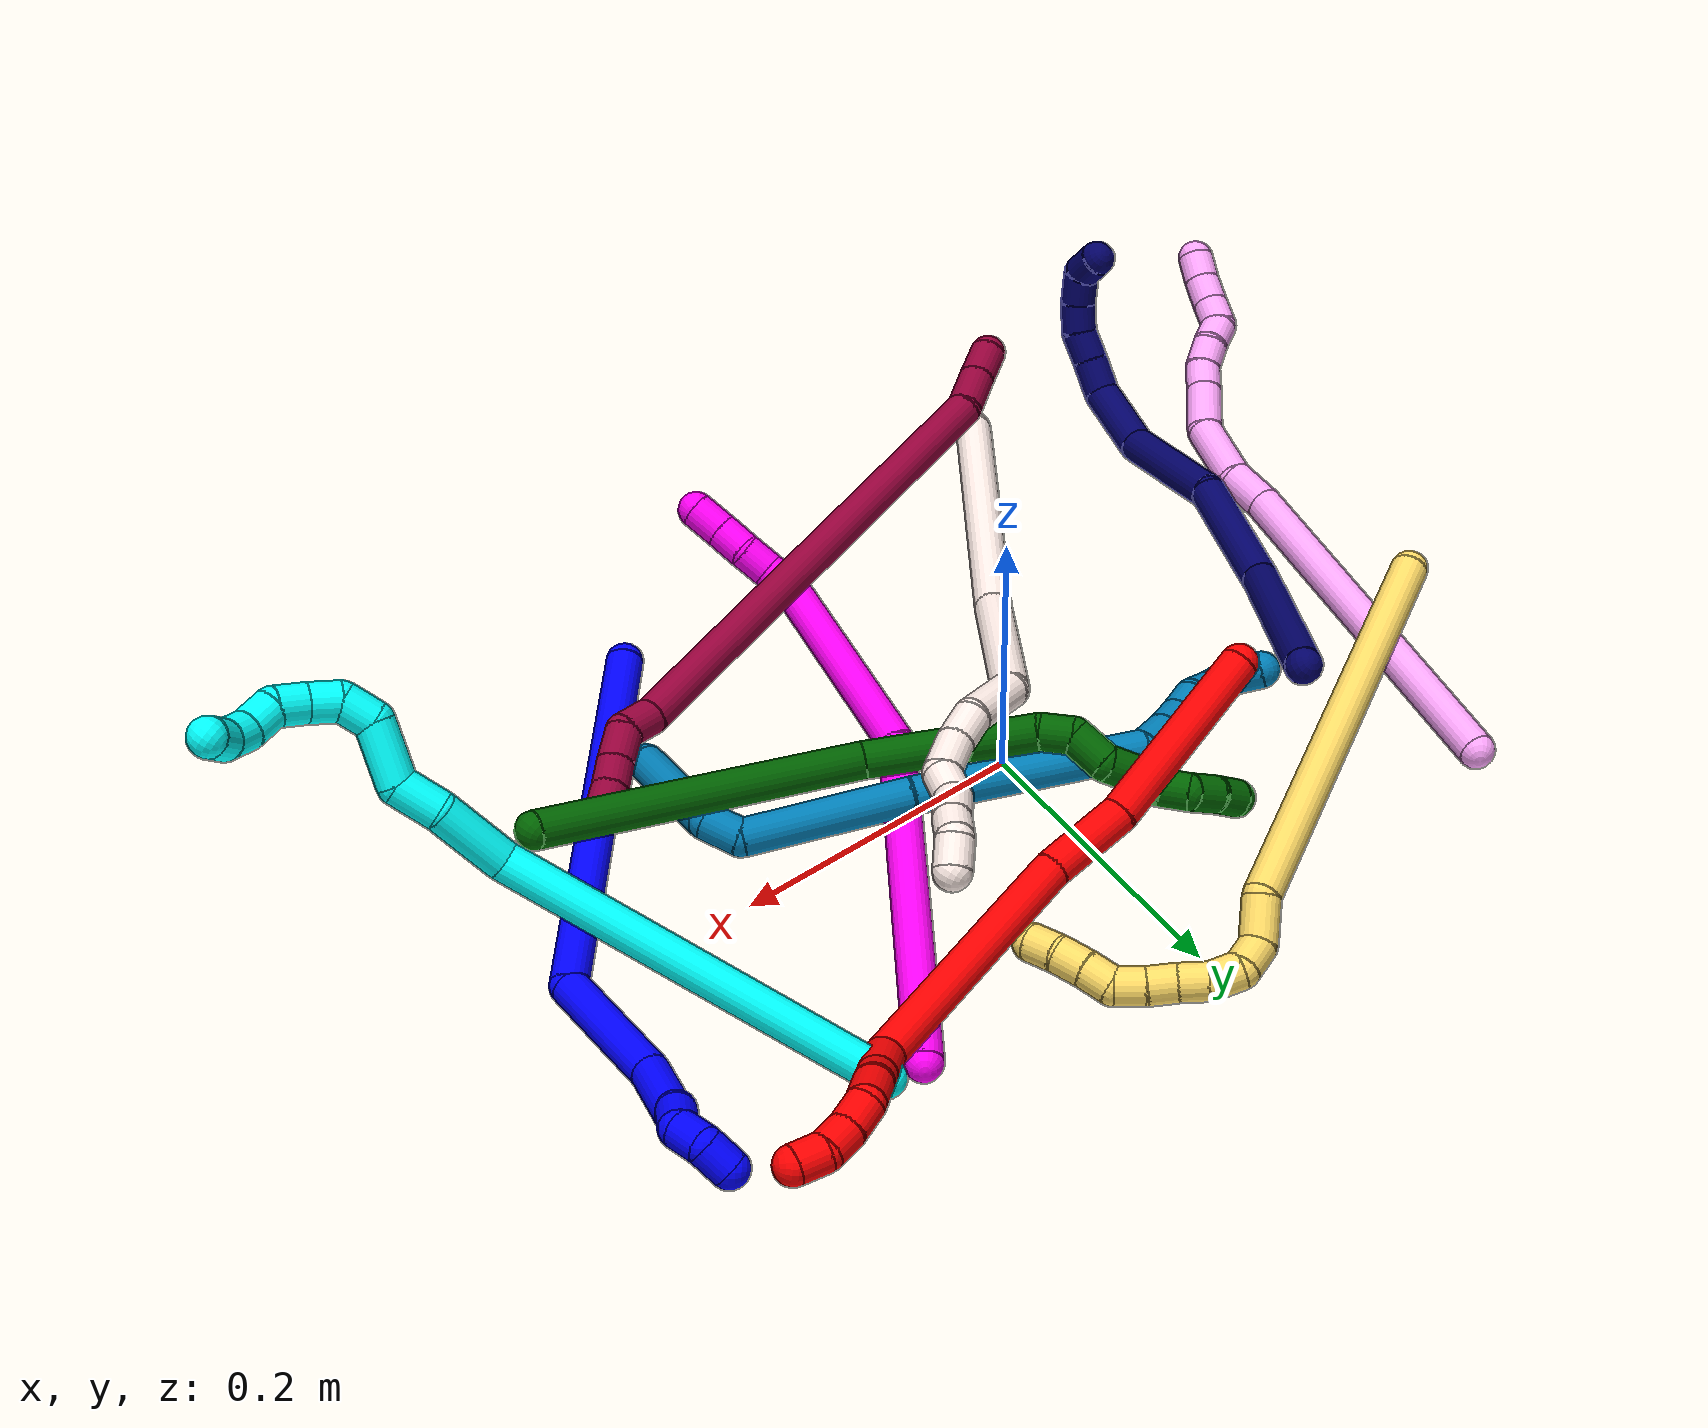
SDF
<sdf version="1.7">
 <world name="default">
  <plugin name="TubeGeneratorPlugin" filename="libtube_generator_plugin.so"/>
  <model name="photoneo_s_sensor">
   <static>1</static>
   <pose>0 0 2 1.57079 1.57079 3.14159</pose>
   <link name="link">
    <inertial><mass>0.1</mass></inertial>
    <sensor name="sensor" type="depth">
     <update_rate>30</update_rate>
     <camera>
      <horizontal_fov>1.22</horizontal_fov>
      <image><width>1920</width><height>1200</height><format>B8G8R8</format></image>
      <clip><near>0.1</near><far>4</far></clip>
      <depth_camera><output>points</output></depth_camera>
     </camera>
     <plugin name="camera_plugin" filename="libgazebo_ros_depth_camera.so">
      <baseline>0.2</baseline>
      <alwaysOn>1</alwaysOn>
      <updateRate>0.0</updateRate>
      <cameraName>camera_ir</cameraName>
      <imageTopicName>/camera/color/image_raw</imageTopicName>
      <cameraInfoTopicName>/camera/color/camera_info</cameraInfoTopicName>
      <depthImageTopicName>/camera/depth/image_raw</depthImageTopicName>
      <depthImageCameraInfoTopicName>/camera/depth/camera_info</depthImageCameraInfoTopicName>
      <pointCloudTopicName>/camera/depth/points</pointCloudTopicName>
      <frameName>fr_optical</frameName>
      <pointCloudCutoff>0.1</pointCloudCutoff>
      <pointCloudCutoffMax>2.0</pointCloudCutoffMax>
      <distortionK1>0</distortionK1>
      <distortionK2>0</distortionK2>
      <distortionK3>0</distortionK3>
      <distortionT1>0</distortionT1>
      <distortionT2>0</distortionT2>
      <CxPrime>0</CxPrime>
      <Cx>0</Cx>
      <Cy>0</Cy>
      <focalLength>0</focalLength>
      <hackBaseline>0</hackBaseline>
     </plugin>
    </sensor>
   </link>
  </model>
  <gravity>0 0 -9.8</gravity>
  <magnetic_field>6e-06 2.3e-05 -4.2e-05</magnetic_field>
  <atmosphere type="adiabatic"/>
  <physics name="default_physics" default="0" type="ode">
   <max_step_size>0.003</max_step_size>
   <real_time_factor>1</real_time_factor>
   <real_time_update_rate>1000</real_time_update_rate>
   <max_contacts>10000</max_contacts>
   <ode>
    <solver>
     <type>quick</type>
     <iters>100</iters>
     <sor>1.3</sor>
     <use_dynamic_moi_rescaling>0</use_dynamic_moi_rescaling>
    </solver>
    <constraints>
     <contact_max_correcting_vel>0</contact_max_correcting_vel>
     <contact_surface_layer>0.001</contact_surface_layer>
     <cfm>0</cfm>
     <erp>0.2</erp>
    </constraints>
   </ode>
  </physics>
  <scene><ambient>0.4 0.4 0.4 1</ambient><background>0.7 0.7 0.7 1</background><shadows>0</shadows></scene>
  <audio><device>default</device></audio>
  <spherical_coordinates>
   <surface_model>EARTH_WGS84</surface_model>
   <latitude_deg>0</latitude_deg>
   <longitude_deg>0</longitude_deg>
   <elevation>0</elevation>
   <heading_deg>0</heading_deg>
  </spherical_coordinates>
  <model name="bin">
   <static>1</static>
   <link name="bottom">
    <collision name="collision-bottom">
     <pose>0 0 -0.01 0 -0 0</pose>
     <geometry><box><size>0.8 0.6 0.02</size></box></geometry>
     <surface>
      <friction><ode><mu>100</mu><mu2>100</mu2></ode></friction>
      <contact><collide_bitmask>65535</collide_bitmask></contact>
     </surface>
    </collision>
   </link>
   <link name="west_wall">
    <collision name="collision-west_wall">
     <pose>-0.41 0 0.1 0 -0 0</pose>
     <geometry><box><size>0.02 0.6 0.2</size></box></geometry>
     <surface>
      <friction><ode><mu>100</mu><mu2>100</mu2></ode></friction>
      <contact><collide_bitmask>65535</collide_bitmask></contact>
     </surface>
    </collision>
   </link>
   <link name="east_wall">
    <collision name="collision-east_wall">
     <pose>0.41 0 0.1 0 -0 0</pose>
     <geometry><box><size>0.02 0.6 0.2</size></box></geometry>
     <surface>
      <friction><ode><mu>100</mu><mu2>100</mu2></ode></friction>
      <contact><collide_bitmask>65535</collide_bitmask></contact>
     </surface>
    </collision>
   </link>
   <link name="south_wall">
    <collision name="collision-south_wall">
     <pose>0 -0.31 0.1 0 -0 0</pose>
     <geometry><box><size>0.8 0.02 0.2</size></box></geometry>
     <surface>
      <friction><ode><mu>100</mu><mu2>100</mu2></ode></friction>
      <contact><collide_bitmask>65535</collide_bitmask></contact>
     </surface>
    </collision>
   </link>
   <link name="north_wall">
    <collision name="collision-north_wall">
     <pose>0 0.31 0.1 0 -0 0</pose>
     <geometry><box><size>0.8 0.02 0.2</size></box></geometry>
     <surface>
      <friction><ode><mu>100</mu><mu2>100</mu2></ode></friction>
      <contact><collide_bitmask>65535</collide_bitmask></contact>
     </surface>
    </collision>
   </link>
  </model>
  <model name="1">
   <static>0</static>
   <link name="1">
    <collision name="collision-cylinder-e_1_1_4">
     <pose>-0.120288 0.064847 -0.00699 -1.67818 -1.07395 1.17084</pose>
     <geometry><cylinder><radius>0.0125</radius><length>0.273664</length></cylinder></geometry>
     <surface>
      <friction><ode><mu>1.16</mu><mu2>1.16</mu2><slip1>0</slip1><slip2>0</slip2></ode></friction>
      <contact><ode><kp>1e+06</kp><kd>1</kd><max_vel>0</max_vel><min_depth>0.001</min_depth></ode></contact>
     </surface>
    </collision>
    <visual name="visual-cylinder-e_1_1_4">
     <pose>-0.120288 0.064847 -0.00699 -1.67818 -1.07395 1.17084</pose>
     <geometry><cylinder><radius>0.0125</radius><length>0.273664</length></cylinder></geometry>
     <material><ambient>0 0 1 1</ambient></material>
    </visual>
    <collision name="collision-cylinder-e_2_4_5">
     <pose>-0.268102 0.146072 0.012988 -0.545803 -0.717363 0.209091</pose>
     <geometry><cylinder><radius>0.0125</radius><length>0.083744</length></cylinder></geometry>
     <surface>
      <friction><ode><mu>1.16</mu><mu2>1.16</mu2><slip1>0</slip1><slip2>0</slip2></ode></friction>
      <contact><ode><kp>1e+06</kp><kd>1</kd><max_vel>0</max_vel><min_depth>0.001</min_depth></ode></contact>
     </surface>
    </collision>
    <visual name="visual-cylinder-e_2_4_5">
     <pose>-0.268102 0.146072 0.012988 -0.545803 -0.717363 0.209091</pose>
     <geometry><cylinder><radius>0.0125</radius><length>0.083744</length></cylinder></geometry>
     <material><ambient>0 0 1 1</ambient></material>
    </visual>
    <collision name="collision-cylinder-e_3_5_6">
     <pose>-0.311178 0.180634 0.049346 -1.09414 -0.649756 0.404675</pose>
     <geometry><cylinder><radius>0.0125</radius><length>0.051403</length></cylinder></geometry>
     <surface>
      <friction><ode><mu>1.16</mu><mu2>1.16</mu2><slip1>0</slip1><slip2>0</slip2></ode></friction>
      <contact><ode><kp>1e+06</kp><kd>1</kd><max_vel>0</max_vel><min_depth>0.001</min_depth></ode></contact>
     </surface>
    </collision>
    <visual name="visual-cylinder-e_3_5_6">
     <pose>-0.311178 0.180634 0.049346 -1.09414 -0.649756 0.404675</pose>
     <geometry><cylinder><radius>0.0125</radius><length>0.051403</length></cylinder></geometry>
     <material><ambient>0 0 1 1</ambient></material>
    </visual>
    <collision name="collision-cylinder-e_4_6_7">
     <pose>-0.326707 0.213772 0.059341 -1.53027 0.001316 -0.001264</pose>
     <geometry><cylinder><radius>0.0125</radius><length>0.029933</length></cylinder></geometry>
     <surface>
      <friction><ode><mu>1.16</mu><mu2>1.16</mu2><slip1>0</slip1><slip2>0</slip2></ode></friction>
      <contact><ode><kp>1e+06</kp><kd>1</kd><max_vel>0</max_vel><min_depth>0.001</min_depth></ode></contact>
     </surface>
    </collision>
    <visual name="visual-cylinder-e_4_6_7">
     <pose>-0.326707 0.213772 0.059341 -1.53027 0.001316 -0.001264</pose>
     <geometry><cylinder><radius>0.0125</radius><length>0.029933</length></cylinder></geometry>
     <material><ambient>0 0 1 1</ambient></material>
    </visual>
    <collision name="collision-cylinder-e_5_7_8">
     <pose>-0.332744 0.237209 0.061269 -1.41629 -0.614395 0.53051</pose>
     <geometry><cylinder><radius>0.0125</radius><length>0.021013</length></cylinder></geometry>
     <surface>
      <friction><ode><mu>1.16</mu><mu2>1.16</mu2><slip1>0</slip1><slip2>0</slip2></ode></friction>
      <contact><ode><kp>1e+06</kp><kd>1</kd><max_vel>0</max_vel><min_depth>0.001</min_depth></ode></contact>
     </surface>
    </collision>
    <visual name="visual-cylinder-e_5_7_8">
     <pose>-0.332744 0.237209 0.061269 -1.41629 -0.614395 0.53051</pose>
     <geometry><cylinder><radius>0.0125</radius><length>0.021013</length></cylinder></geometry>
     <material><ambient>0 0 1 1</ambient></material>
    </visual>
    <collision name="collision-cylinder-e_6_8_9">
     <pose>-0.343867 0.24983 0.070196 -0.49828 -0.529399 0.137711</pose>
     <geometry><cylinder><radius>0.0125</radius><length>0.020064</length></cylinder></geometry>
     <surface>
      <friction><ode><mu>1.16</mu><mu2>1.16</mu2><slip1>0</slip1><slip2>0</slip2></ode></friction>
      <contact><ode><kp>1e+06</kp><kd>1</kd><max_vel>0</max_vel><min_depth>0.001</min_depth></ode></contact>
     </surface>
    </collision>
    <visual name="visual-cylinder-e_6_8_9">
     <pose>-0.343867 0.24983 0.070196 -0.49828 -0.529399 0.137711</pose>
     <geometry><cylinder><radius>0.0125</radius><length>0.020064</length></cylinder></geometry>
     <material><ambient>0 0 1 1</ambient></material>
    </visual>
    <collision name="collision-cylinder-e_7_9_2">
     <pose>-0.3551 0.251489 0.085393 0.315646 -0.657504 -0.108473</pose>
     <geometry><cylinder><radius>0.0125</radius><length>0.020179</length></cylinder></geometry>
     <surface>
      <friction><ode><mu>1.16</mu><mu2>1.16</mu2><slip1>0</slip1><slip2>0</slip2></ode></friction>
      <contact><ode><kp>1e+06</kp><kd>1</kd><max_vel>0</max_vel><min_depth>0.001</min_depth></ode></contact>
     </surface>
    </collision>
    <visual name="visual-cylinder-e_7_9_2">
     <pose>-0.3551 0.251489 0.085393 0.315646 -0.657504 -0.108473</pose>
     <geometry><cylinder><radius>0.0125</radius><length>0.020179</length></cylinder></geometry>
     <material><ambient>0 0 1 1</ambient></material>
    </visual>
    <collision name="collision-sphere-2">
     <pose>-0.361266 0.24901 0.092984 0 -0 0</pose>
     <geometry><sphere><radius>0.0125</radius></sphere></geometry>
     <surface>
      <friction><ode><mu>1.16</mu><mu2>1.16</mu2><slip1>0</slip1><slip2>0</slip2></ode></friction>
      <contact><ode><kp>1e+06</kp><kd>1</kd><max_vel>0</max_vel><min_depth>0.001</min_depth></ode></contact>
     </surface>
    </collision>
    <visual name="visual-sphere-2">
     <pose>-0.361266 0.24901 0.092984 0 -0 0</pose>
     <geometry><sphere><radius>0.0125</radius></sphere></geometry>
     <material><ambient>0 0 1 1</ambient></material>
    </visual>
    <collision name="collision-sphere-9">
     <pose>-0.348934 0.253968 0.077802 0 -0 0</pose>
     <geometry><sphere><radius>0.0125</radius></sphere></geometry>
     <surface>
      <friction><ode><mu>1.16</mu><mu2>1.16</mu2><slip1>0</slip1><slip2>0</slip2></ode></friction>
      <contact><ode><kp>1e+06</kp><kd>1</kd><max_vel>0</max_vel><min_depth>0.001</min_depth></ode></contact>
     </surface>
    </collision>
    <visual name="visual-sphere-9">
     <pose>-0.348934 0.253968 0.077802 0 -0 0</pose>
     <geometry><sphere><radius>0.0125</radius></sphere></geometry>
     <material><ambient>0 0 1 1</ambient></material>
    </visual>
    <collision name="collision-sphere-4">
     <pose>-0.240575 0.129693 -0.01398 0 -0 0</pose>
     <geometry><sphere><radius>0.0125</radius></sphere></geometry>
     <surface>
      <friction><ode><mu>1.16</mu><mu2>1.16</mu2><slip1>0</slip1><slip2>0</slip2></ode></friction>
      <contact><ode><kp>1e+06</kp><kd>1</kd><max_vel>0</max_vel><min_depth>0.001</min_depth></ode></contact>
     </surface>
    </collision>
    <visual name="visual-sphere-4">
     <pose>-0.240575 0.129693 -0.01398 0 -0 0</pose>
     <geometry><sphere><radius>0.0125</radius></sphere></geometry>
     <material><ambient>0 0 1 1</ambient></material>
    </visual>
    <collision name="collision-sphere-1">
     <geometry><sphere><radius>0.0125</radius></sphere></geometry>
     <surface>
      <friction><ode><mu>1.16</mu><mu2>1.16</mu2><slip1>0</slip1><slip2>0</slip2></ode></friction>
      <contact><ode><kp>1e+06</kp><kd>1</kd><max_vel>0</max_vel><min_depth>0.001</min_depth></ode></contact>
     </surface>
    </collision>
    <visual name="visual-sphere-1">
     <geometry><sphere><radius>0.0125</radius></sphere></geometry>
     <material><ambient>0 0 1 1</ambient></material>
    </visual>
    <collision name="collision-sphere-8">
     <pose>-0.338801 0.245691 0.06259 0 -0 0</pose>
     <geometry><sphere><radius>0.0125</radius></sphere></geometry>
     <surface>
      <friction><ode><mu>1.16</mu><mu2>1.16</mu2><slip1>0</slip1><slip2>0</slip2></ode></friction>
      <contact><ode><kp>1e+06</kp><kd>1</kd><max_vel>0</max_vel><min_depth>0.001</min_depth></ode></contact>
     </surface>
    </collision>
    <visual name="visual-sphere-8">
     <pose>-0.338801 0.245691 0.06259 0 -0 0</pose>
     <geometry><sphere><radius>0.0125</radius></sphere></geometry>
     <material><ambient>0 0 1 1</ambient></material>
    </visual>
    <collision name="collision-sphere-5">
     <pose>-0.295629 0.162451 0.039956 0 -0 0</pose>
     <geometry><sphere><radius>0.0125</radius></sphere></geometry>
     <surface>
      <friction><ode><mu>1.16</mu><mu2>1.16</mu2><slip1>0</slip1><slip2>0</slip2></ode></friction>
      <contact><ode><kp>1e+06</kp><kd>1</kd><max_vel>0</max_vel><min_depth>0.001</min_depth></ode></contact>
     </surface>
    </collision>
    <visual name="visual-sphere-5">
     <pose>-0.295629 0.162451 0.039956 0 -0 0</pose>
     <geometry><sphere><radius>0.0125</radius></sphere></geometry>
     <material><ambient>0 0 1 1</ambient></material>
    </visual>
    <collision name="collision-sphere-6">
     <pose>-0.326727 0.198817 0.058735 0 -0 0</pose>
     <geometry><sphere><radius>0.0125</radius></sphere></geometry>
     <surface>
      <friction><ode><mu>1.16</mu><mu2>1.16</mu2><slip1>0</slip1><slip2>0</slip2></ode></friction>
      <contact><ode><kp>1e+06</kp><kd>1</kd><max_vel>0</max_vel><min_depth>0.001</min_depth></ode></contact>
     </surface>
    </collision>
    <visual name="visual-sphere-6">
     <pose>-0.326727 0.198817 0.058735 0 -0 0</pose>
     <geometry><sphere><radius>0.0125</radius></sphere></geometry>
     <material><ambient>0 0 1 1</ambient></material>
    </visual>
    <collision name="collision-sphere-7">
     <pose>-0.326688 0.228726 0.059948 0 -0 0</pose>
     <geometry><sphere><radius>0.0125</radius></sphere></geometry>
     <surface>
      <friction><ode><mu>1.16</mu><mu2>1.16</mu2><slip1>0</slip1><slip2>0</slip2></ode></friction>
      <contact><ode><kp>1e+06</kp><kd>1</kd><max_vel>0</max_vel><min_depth>0.001</min_depth></ode></contact>
     </surface>
    </collision>
    <visual name="visual-sphere-7">
     <pose>-0.326688 0.228726 0.059948 0 -0 0</pose>
     <geometry><sphere><radius>0.0125</radius></sphere></geometry>
     <material><ambient>0 0 1 1</ambient></material>
    </visual>
    <inertial>
     <pose>-0.204404 0.121469 0.015813 0 -0 0</pose>
     <mass>0.5</mass>
     <inertia>
      <ixx>0.001114</ixx>
      <ixy>0</ixy>
      <ixz>0</ixz>
      <iyy>0.002158</iyy>
      <iyz>0</iyz>
      <izz>0.000714</izz>
     </inertia>
    </inertial>
   </link>
   <pose>0.149707 -0.219974 0.00636 1.62249 -0.497248 -2.24902</pose>
  </model>
  <model name="2">
   <static>0</static>
   <link name="2">
    <collision name="collision-cylinder-e_1_1_4">
     <pose>0.010645 0.046514 -0.044688 -2.33618 0.163554 -0.380154</pose>
     <geometry><cylinder><radius>0.0125</radius><length>0.130749</length></cylinder></geometry>
     <surface>
      <friction><ode><mu>1.16</mu><mu2>1.16</mu2><slip1>0</slip1><slip2>0</slip2></ode></friction>
      <contact><ode><kp>1e+06</kp><kd>1</kd><max_vel>0</max_vel><min_depth>0.001</min_depth></ode></contact>
     </surface>
    </collision>
    <visual name="visual-cylinder-e_1_1_4">
     <pose>0.010645 0.046514 -0.044688 -2.33618 0.163554 -0.380154</pose>
     <geometry><cylinder><radius>0.0125</radius><length>0.130749</length></cylinder></geometry>
     <material><ambient>1 0 0 1</ambient></material>
    </visual>
    <collision name="collision-cylinder-e_2_4_5">
     <pose>0.025008 0.109495 -0.112997 -2.53276 0.128441 -0.403797</pose>
     <geometry><cylinder><radius>0.0125</radius><length>0.058067</length></cylinder></geometry>
     <surface>
      <friction><ode><mu>1.16</mu><mu2>1.16</mu2><slip1>0</slip1><slip2>0</slip2></ode></friction>
      <contact><ode><kp>1e+06</kp><kd>1</kd><max_vel>0</max_vel><min_depth>0.001</min_depth></ode></contact>
     </surface>
    </collision>
    <visual name="visual-cylinder-e_2_4_5">
     <pose>0.025008 0.109495 -0.112997 -2.53276 0.128441 -0.403797</pose>
     <geometry><cylinder><radius>0.0125</radius><length>0.058067</length></cylinder></geometry>
     <material><ambient>1 0 0 1</ambient></material>
    </visual>
    <collision name="collision-cylinder-e_3_5_6">
     <pose>0.053768 0.176598 -0.19864 -2.45694 0.303113 -0.809794</pose>
     <geometry><cylinder><radius>0.0125</radius><length>0.167785</length></cylinder></geometry>
     <surface>
      <friction><ode><mu>1.16</mu><mu2>1.16</mu2><slip1>0</slip1><slip2>0</slip2></ode></friction>
      <contact><ode><kp>1e+06</kp><kd>1</kd><max_vel>0</max_vel><min_depth>0.001</min_depth></ode></contact>
     </surface>
    </collision>
    <visual name="visual-cylinder-e_3_5_6">
     <pose>0.053768 0.176598 -0.19864 -2.45694 0.303113 -0.809794</pose>
     <geometry><cylinder><radius>0.0125</radius><length>0.167785</length></cylinder></geometry>
     <material><ambient>1 0 0 1</ambient></material>
    </visual>
    <collision name="collision-cylinder-e_4_6_7">
     <pose>0.093809 0.230402 -0.26849 -2.75689 1.05812 -2.49847</pose>
     <geometry><cylinder><radius>0.0125</radius><length>0.034425</length></cylinder></geometry>
     <surface>
      <friction><ode><mu>1.16</mu><mu2>1.16</mu2><slip1>0</slip1><slip2>0</slip2></ode></friction>
      <contact><ode><kp>1e+06</kp><kd>1</kd><max_vel>0</max_vel><min_depth>0.001</min_depth></ode></contact>
     </surface>
    </collision>
    <visual name="visual-cylinder-e_4_6_7">
     <pose>0.093809 0.230402 -0.26849 -2.75689 1.05812 -2.49847</pose>
     <geometry><cylinder><radius>0.0125</radius><length>0.034425</length></cylinder></geometry>
     <material><ambient>1 0 0 1</ambient></material>
    </visual>
    <collision name="collision-cylinder-e_5_7_8">
     <pose>0.117938 0.233942 -0.280535 -3.05401 1.13634 -3.00453</pose>
     <geometry><cylinder><radius>0.0125</radius><length>0.020128</length></cylinder></geometry>
     <surface>
      <friction><ode><mu>1.16</mu><mu2>1.16</mu2><slip1>0</slip1><slip2>0</slip2></ode></friction>
      <contact><ode><kp>1e+06</kp><kd>1</kd><max_vel>0</max_vel><min_depth>0.001</min_depth></ode></contact>
     </surface>
    </collision>
    <visual name="visual-cylinder-e_5_7_8">
     <pose>0.117938 0.233942 -0.280535 -3.05401 1.13634 -3.00453</pose>
     <geometry><cylinder><radius>0.0125</radius><length>0.020128</length></cylinder></geometry>
     <material><ambient>1 0 0 1</ambient></material>
    </visual>
    <collision name="collision-cylinder-e_6_8_9">
     <pose>0.138844 0.237708 -0.291074 -2.64845 1.02368 -2.29917</pose>
     <geometry><cylinder><radius>0.0125</radius><length>0.027579</length></cylinder></geometry>
     <surface>
      <friction><ode><mu>1.16</mu><mu2>1.16</mu2><slip1>0</slip1><slip2>0</slip2></ode></friction>
      <contact><ode><kp>1e+06</kp><kd>1</kd><max_vel>0</max_vel><min_depth>0.001</min_depth></ode></contact>
     </surface>
    </collision>
    <visual name="visual-cylinder-e_6_8_9">
     <pose>0.138844 0.237708 -0.291074 -2.64845 1.02368 -2.29917</pose>
     <geometry><cylinder><radius>0.0125</radius><length>0.027579</length></cylinder></geometry>
     <material><ambient>1 0 0 1</ambient></material>
    </visual>
    <collision name="collision-cylinder-e_7_9_10">
     <pose>0.155311 0.247488 -0.304432 -2.40497 0.458488 -1.08766</pose>
     <geometry><cylinder><radius>0.0125</radius><length>0.021195</length></cylinder></geometry>
     <surface>
      <friction><ode><mu>1.16</mu><mu2>1.16</mu2><slip1>0</slip1><slip2>0</slip2></ode></friction>
      <contact><ode><kp>1e+06</kp><kd>1</kd><max_vel>0</max_vel><min_depth>0.001</min_depth></ode></contact>
     </surface>
    </collision>
    <visual name="visual-cylinder-e_7_9_10">
     <pose>0.155311 0.247488 -0.304432 -2.40497 0.458488 -1.08766</pose>
     <geometry><cylinder><radius>0.0125</radius><length>0.021195</length></cylinder></geometry>
     <material><ambient>1 0 0 1</ambient></material>
    </visual>
    <collision name="collision-cylinder-e_8_10_11">
     <pose>0.164059 0.258804 -0.319196 -2.57332 0.416847 -1.25357</pose>
     <geometry><cylinder><radius>0.0125</radius><length>0.020046</length></cylinder></geometry>
     <surface>
      <friction><ode><mu>1.16</mu><mu2>1.16</mu2><slip1>0</slip1><slip2>0</slip2></ode></friction>
      <contact><ode><kp>1e+06</kp><kd>1</kd><max_vel>0</max_vel><min_depth>0.001</min_depth></ode></contact>
     </surface>
    </collision>
    <visual name="visual-cylinder-e_8_10_11">
     <pose>0.164059 0.258804 -0.319196 -2.57332 0.416847 -1.25357</pose>
     <geometry><cylinder><radius>0.0125</radius><length>0.020046</length></cylinder></geometry>
     <material><ambient>1 0 0 1</ambient></material>
    </visual>
    <collision name="collision-cylinder-e_9_11_2">
     <pose>0.168739 0.266958 -0.33638 -2.81341 0.062116 -0.37095</pose>
     <geometry><cylinder><radius>0.0125</radius><length>0.020026</length></cylinder></geometry>
     <surface>
      <friction><ode><mu>1.16</mu><mu2>1.16</mu2><slip1>0</slip1><slip2>0</slip2></ode></friction>
      <contact><ode><kp>1e+06</kp><kd>1</kd><max_vel>0</max_vel><min_depth>0.001</min_depth></ode></contact>
     </surface>
    </collision>
    <visual name="visual-cylinder-e_9_11_2">
     <pose>0.168739 0.266958 -0.33638 -2.81341 0.062116 -0.37095</pose>
     <geometry><cylinder><radius>0.0125</radius><length>0.020026</length></cylinder></geometry>
     <material><ambient>1 0 0 1</ambient></material>
    </visual>
    <collision name="collision-sphere-2">
     <pose>0.16936 0.270179 -0.345841 0 -0 0</pose>
     <geometry><sphere><radius>0.0125</radius></sphere></geometry>
     <surface>
      <friction><ode><mu>1.16</mu><mu2>1.16</mu2><slip1>0</slip1><slip2>0</slip2></ode></friction>
      <contact><ode><kp>1e+06</kp><kd>1</kd><max_vel>0</max_vel><min_depth>0.001</min_depth></ode></contact>
     </surface>
    </collision>
    <visual name="visual-sphere-2">
     <pose>0.16936 0.270179 -0.345841 0 -0 0</pose>
     <geometry><sphere><radius>0.0125</radius></sphere></geometry>
     <material><ambient>1 0 0 1</ambient></material>
    </visual>
    <collision name="collision-sphere-11">
     <pose>0.168117 0.263736 -0.32692 0 -0 0</pose>
     <geometry><sphere><radius>0.0125</radius></sphere></geometry>
     <surface>
      <friction><ode><mu>1.16</mu><mu2>1.16</mu2><slip1>0</slip1><slip2>0</slip2></ode></friction>
      <contact><ode><kp>1e+06</kp><kd>1</kd><max_vel>0</max_vel><min_depth>0.001</min_depth></ode></contact>
     </surface>
    </collision>
    <visual name="visual-sphere-11">
     <pose>0.168117 0.263736 -0.32692 0 -0 0</pose>
     <geometry><sphere><radius>0.0125</radius></sphere></geometry>
     <material><ambient>1 0 0 1</ambient></material>
    </visual>
    <collision name="collision-sphere-10">
     <pose>0.160001 0.253872 -0.311472 0 -0 0</pose>
     <geometry><sphere><radius>0.0125</radius></sphere></geometry>
     <surface>
      <friction><ode><mu>1.16</mu><mu2>1.16</mu2><slip1>0</slip1><slip2>0</slip2></ode></friction>
      <contact><ode><kp>1e+06</kp><kd>1</kd><max_vel>0</max_vel><min_depth>0.001</min_depth></ode></contact>
     </surface>
    </collision>
    <visual name="visual-sphere-10">
     <pose>0.160001 0.253872 -0.311472 0 -0 0</pose>
     <geometry><sphere><radius>0.0125</radius></sphere></geometry>
     <material><ambient>1 0 0 1</ambient></material>
    </visual>
    <collision name="collision-sphere-9">
     <pose>0.15062 0.241104 -0.297393 0 -0 0</pose>
     <geometry><sphere><radius>0.0125</radius></sphere></geometry>
     <surface>
      <friction><ode><mu>1.16</mu><mu2>1.16</mu2><slip1>0</slip1><slip2>0</slip2></ode></friction>
      <contact><ode><kp>1e+06</kp><kd>1</kd><max_vel>0</max_vel><min_depth>0.001</min_depth></ode></contact>
     </surface>
    </collision>
    <visual name="visual-sphere-9">
     <pose>0.15062 0.241104 -0.297393 0 -0 0</pose>
     <geometry><sphere><radius>0.0125</radius></sphere></geometry>
     <material><ambient>1 0 0 1</ambient></material>
    </visual>
    <collision name="collision-sphere-4">
     <pose>0.021289 0.093027 -0.089376 0 -0 0</pose>
     <geometry><sphere><radius>0.0125</radius></sphere></geometry>
     <surface>
      <friction><ode><mu>1.16</mu><mu2>1.16</mu2><slip1>0</slip1><slip2>0</slip2></ode></friction>
      <contact><ode><kp>1e+06</kp><kd>1</kd><max_vel>0</max_vel><min_depth>0.001</min_depth></ode></contact>
     </surface>
    </collision>
    <visual name="visual-sphere-4">
     <pose>0.021289 0.093027 -0.089376 0 -0 0</pose>
     <geometry><sphere><radius>0.0125</radius></sphere></geometry>
     <material><ambient>1 0 0 1</ambient></material>
    </visual>
    <collision name="collision-sphere-1">
     <geometry><sphere><radius>0.0125</radius></sphere></geometry>
     <surface>
      <friction><ode><mu>1.16</mu><mu2>1.16</mu2><slip1>0</slip1><slip2>0</slip2></ode></friction>
      <contact><ode><kp>1e+06</kp><kd>1</kd><max_vel>0</max_vel><min_depth>0.001</min_depth></ode></contact>
     </surface>
    </collision>
    <visual name="visual-sphere-1">
     <geometry><sphere><radius>0.0125</radius></sphere></geometry>
     <material><ambient>1 0 0 1</ambient></material>
    </visual>
    <collision name="collision-sphere-8">
     <pose>0.127067 0.234312 -0.284755 0 -0 0</pose>
     <geometry><sphere><radius>0.0125</radius></sphere></geometry>
     <surface>
      <friction><ode><mu>1.16</mu><mu2>1.16</mu2><slip1>0</slip1><slip2>0</slip2></ode></friction>
      <contact><ode><kp>1e+06</kp><kd>1</kd><max_vel>0</max_vel><min_depth>0.001</min_depth></ode></contact>
     </surface>
    </collision>
    <visual name="visual-sphere-8">
     <pose>0.127067 0.234312 -0.284755 0 -0 0</pose>
     <geometry><sphere><radius>0.0125</radius></sphere></geometry>
     <material><ambient>1 0 0 1</ambient></material>
    </visual>
    <collision name="collision-sphere-5">
     <pose>0.028727 0.125963 -0.136617 0 -0 0</pose>
     <geometry><sphere><radius>0.0125</radius></sphere></geometry>
     <surface>
      <friction><ode><mu>1.16</mu><mu2>1.16</mu2><slip1>0</slip1><slip2>0</slip2></ode></friction>
      <contact><ode><kp>1e+06</kp><kd>1</kd><max_vel>0</max_vel><min_depth>0.001</min_depth></ode></contact>
     </surface>
    </collision>
    <visual name="visual-sphere-5">
     <pose>0.028727 0.125963 -0.136617 0 -0 0</pose>
     <geometry><sphere><radius>0.0125</radius></sphere></geometry>
     <material><ambient>1 0 0 1</ambient></material>
    </visual>
    <collision name="collision-sphere-6">
     <pose>0.07881 0.227234 -0.260664 0 -0 0</pose>
     <geometry><sphere><radius>0.0125</radius></sphere></geometry>
     <surface>
      <friction><ode><mu>1.16</mu><mu2>1.16</mu2><slip1>0</slip1><slip2>0</slip2></ode></friction>
      <contact><ode><kp>1e+06</kp><kd>1</kd><max_vel>0</max_vel><min_depth>0.001</min_depth></ode></contact>
     </surface>
    </collision>
    <visual name="visual-sphere-6">
     <pose>0.07881 0.227234 -0.260664 0 -0 0</pose>
     <geometry><sphere><radius>0.0125</radius></sphere></geometry>
     <material><ambient>1 0 0 1</ambient></material>
    </visual>
    <collision name="collision-sphere-7">
     <pose>0.108809 0.233571 -0.276316 0 -0 0</pose>
     <geometry><sphere><radius>0.0125</radius></sphere></geometry>
     <surface>
      <friction><ode><mu>1.16</mu><mu2>1.16</mu2><slip1>0</slip1><slip2>0</slip2></ode></friction>
      <contact><ode><kp>1e+06</kp><kd>1</kd><max_vel>0</max_vel><min_depth>0.001</min_depth></ode></contact>
     </surface>
    </collision>
    <visual name="visual-sphere-7">
     <pose>0.108809 0.233571 -0.276316 0 -0 0</pose>
     <geometry><sphere><radius>0.0125</radius></sphere></geometry>
     <material><ambient>1 0 0 1</ambient></material>
    </visual>
    <inertial>
     <pose>0.062515 0.154092 -0.176475 0 -0 0</pose>
     <mass>0.5</mass>
     <inertia>
      <ixx>0.000108</ixx>
      <ixy>0</ixy>
      <ixz>0</ixz>
      <iyy>-0.000619</iyy>
      <iyz>0</iyz>
      <izz>-0.000581</izz>
     </inertia>
    </inertial>
   </link>
   <pose>-0.126413 0.080776 0.085099 -1.90267 -0.68699 1.38925</pose>
  </model>
  <model name="3">
   <static>0</static>
   <link name="3">
    <collision name="collision-cylinder-e_1_1_4">
     <pose>0.011978 0.007342 -0.128714 -3.08462 0.092639 -2.03918</pose>
     <geometry><cylinder><radius>0.0125</radius><length>0.258956</length></cylinder></geometry>
     <surface>
      <friction><ode><mu>1.16</mu><mu2>1.16</mu2><slip1>0</slip1><slip2>0</slip2></ode></friction>
      <contact><ode><kp>1e+06</kp><kd>1</kd><max_vel>0</max_vel><min_depth>0.001</min_depth></ode></contact>
     </surface>
    </collision>
    <visual name="visual-cylinder-e_1_1_4">
     <pose>0.011978 0.007342 -0.128714 -3.08462 0.092639 -2.03918</pose>
     <geometry><cylinder><radius>0.0125</radius><length>0.258956</length></cylinder></geometry>
     <material><ambient>0.003922 1 0.996078 1</ambient></material>
    </visual>
    <collision name="collision-cylinder-e_2_4_5">
     <pose>0.027676 0.005027 -0.280167 2.74003 0.149487 0.705124</pose>
     <geometry><cylinder><radius>0.0125</radius><length>0.049968</length></cylinder></geometry>
     <surface>
      <friction><ode><mu>1.16</mu><mu2>1.16</mu2><slip1>0</slip1><slip2>0</slip2></ode></friction>
      <contact><ode><kp>1e+06</kp><kd>1</kd><max_vel>0</max_vel><min_depth>0.001</min_depth></ode></contact>
     </surface>
    </collision>
    <visual name="visual-cylinder-e_2_4_5">
     <pose>0.027676 0.005027 -0.280167 2.74003 0.149487 0.705124</pose>
     <geometry><cylinder><radius>0.0125</radius><length>0.049968</length></cylinder></geometry>
     <material><ambient>0.003922 1 0.996078 1</ambient></material>
    </visual>
    <collision name="collision-cylinder-e_3_5_6">
     <pose>0.033183 -0.005691 -0.317109 3.06696 0.124774 2.06422</pose>
     <geometry><cylinder><radius>0.0125</radius><length>0.028705</length></cylinder></geometry>
     <surface>
      <friction><ode><mu>1.16</mu><mu2>1.16</mu2><slip1>0</slip1><slip2>0</slip2></ode></friction>
      <contact><ode><kp>1e+06</kp><kd>1</kd><max_vel>0</max_vel><min_depth>0.001</min_depth></ode></contact>
     </surface>
    </collision>
    <visual name="visual-cylinder-e_3_5_6">
     <pose>0.033183 -0.005691 -0.317109 3.06696 0.124774 2.06422</pose>
     <geometry><cylinder><radius>0.0125</radius><length>0.028705</length></cylinder></geometry>
     <material><ambient>0.003922 1 0.996078 1</ambient></material>
    </visual>
    <collision name="collision-cylinder-e_4_6_7">
     <pose>0.026545 -0.014683 -0.347356 2.68258 -0.439908 -1.52684</pose>
     <geometry><cylinder><radius>0.0125</radius><length>0.039564</length></cylinder></geometry>
     <surface>
      <friction><ode><mu>1.16</mu><mu2>1.16</mu2><slip1>0</slip1><slip2>0</slip2></ode></friction>
      <contact><ode><kp>1e+06</kp><kd>1</kd><max_vel>0</max_vel><min_depth>0.001</min_depth></ode></contact>
     </surface>
    </collision>
    <visual name="visual-cylinder-e_4_6_7">
     <pose>0.026545 -0.014683 -0.347356 2.68258 -0.439908 -1.52684</pose>
     <geometry><cylinder><radius>0.0125</radius><length>0.039564</length></cylinder></geometry>
     <material><ambient>0.003922 1 0.996078 1</ambient></material>
    </visual>
    <collision name="collision-cylinder-e_5_7_8">
     <pose>0.019686 -0.023751 -0.37413 3.03593 0.144101 1.87699</pose>
     <geometry><cylinder><radius>0.0125</radius><length>0.021803</length></cylinder></geometry>
     <surface>
      <friction><ode><mu>1.16</mu><mu2>1.16</mu2><slip1>0</slip1><slip2>0</slip2></ode></friction>
      <contact><ode><kp>1e+06</kp><kd>1</kd><max_vel>0</max_vel><min_depth>0.001</min_depth></ode></contact>
     </surface>
    </collision>
    <visual name="visual-cylinder-e_5_7_8">
     <pose>0.019686 -0.023751 -0.37413 3.03593 0.144101 1.87699</pose>
     <geometry><cylinder><radius>0.0125</radius><length>0.021803</length></cylinder></geometry>
     <material><ambient>0.003922 1 0.996078 1</ambient></material>
    </visual>
    <collision name="collision-cylinder-e_6_8_9">
     <pose>0.027843 -0.023885 -0.392389 -3.00914 0.714599 -2.78994</pose>
     <geometry><cylinder><radius>0.0125</radius><length>0.020117</length></cylinder></geometry>
     <surface>
      <friction><ode><mu>1.16</mu><mu2>1.16</mu2><slip1>0</slip1><slip2>0</slip2></ode></friction>
      <contact><ode><kp>1e+06</kp><kd>1</kd><max_vel>0</max_vel><min_depth>0.001</min_depth></ode></contact>
     </surface>
    </collision>
    <visual name="visual-cylinder-e_6_8_9">
     <pose>0.027843 -0.023885 -0.392389 -3.00914 0.714599 -2.78994</pose>
     <geometry><cylinder><radius>0.0125</radius><length>0.020117</length></cylinder></geometry>
     <material><ambient>0.003922 1 0.996078 1</ambient></material>
    </visual>
    <collision name="collision-cylinder-e_7_9_10">
     <pose>0.042134 -0.024024 -0.40631 2.96463 0.870391 2.76451</pose>
     <geometry><cylinder><radius>0.0125</radius><length>0.02014</length></cylinder></geometry>
     <surface>
      <friction><ode><mu>1.16</mu><mu2>1.16</mu2><slip1>0</slip1><slip2>0</slip2></ode></friction>
      <contact><ode><kp>1e+06</kp><kd>1</kd><max_vel>0</max_vel><min_depth>0.001</min_depth></ode></contact>
     </surface>
    </collision>
    <visual name="visual-cylinder-e_7_9_10">
     <pose>0.042134 -0.024024 -0.40631 2.96463 0.870391 2.76451</pose>
     <geometry><cylinder><radius>0.0125</radius><length>0.02014</length></cylinder></geometry>
     <material><ambient>0.003922 1 0.996078 1</ambient></material>
    </visual>
    <collision name="collision-cylinder-e_8_10_11">
     <pose>0.059879 -0.024159 -0.414119 -2.52436 1.39913 -2.41735</pose>
     <geometry><cylinder><radius>0.0125</radius><length>0.020392</length></cylinder></geometry>
     <surface>
      <friction><ode><mu>1.16</mu><mu2>1.16</mu2><slip1>0</slip1><slip2>0</slip2></ode></friction>
      <contact><ode><kp>1e+06</kp><kd>1</kd><max_vel>0</max_vel><min_depth>0.001</min_depth></ode></contact>
     </surface>
    </collision>
    <visual name="visual-cylinder-e_8_10_11">
     <pose>0.059879 -0.024159 -0.414119 -2.52436 1.39913 -2.41735</pose>
     <geometry><cylinder><radius>0.0125</radius><length>0.020392</length></cylinder></geometry>
     <material><ambient>0.003922 1 0.996078 1</ambient></material>
    </visual>
    <collision name="collision-cylinder-e_9_11_12">
     <pose>0.078783 -0.027429 -0.417646 2.02843 1.07691 1.53002</pose>
     <geometry><cylinder><radius>0.0125</radius><length>0.020119</length></cylinder></geometry>
     <surface>
      <friction><ode><mu>1.16</mu><mu2>1.16</mu2><slip1>0</slip1><slip2>0</slip2></ode></friction>
      <contact><ode><kp>1e+06</kp><kd>1</kd><max_vel>0</max_vel><min_depth>0.001</min_depth></ode></contact>
     </surface>
    </collision>
    <visual name="visual-cylinder-e_9_11_12">
     <pose>0.078783 -0.027429 -0.417646 2.02843 1.07691 1.53002</pose>
     <geometry><cylinder><radius>0.0125</radius><length>0.020119</length></cylinder></geometry>
     <material><ambient>0.003922 1 0.996078 1</ambient></material>
    </visual>
    <collision name="collision-cylinder-e_10_12_2">
     <pose>0.093494 -0.039471 -0.422552 1.91672 0.616851 0.851484</pose>
     <geometry><cylinder><radius>0.0125</radius><length>0.020236</length></cylinder></geometry>
     <surface>
      <friction><ode><mu>1.16</mu><mu2>1.16</mu2><slip1>0</slip1><slip2>0</slip2></ode></friction>
      <contact><ode><kp>1e+06</kp><kd>1</kd><max_vel>0</max_vel><min_depth>0.001</min_depth></ode></contact>
     </surface>
    </collision>
    <visual name="visual-cylinder-e_10_12_2">
     <pose>0.093494 -0.039471 -0.422552 1.91672 0.616851 0.851484</pose>
     <geometry><cylinder><radius>0.0125</radius><length>0.020236</length></cylinder></geometry>
     <material><ambient>0.003922 1 0.996078 1</ambient></material>
    </visual>
    <collision name="collision-sphere-2">
     <pose>0.099347 -0.047236 -0.42535 0 -0 0</pose>
     <geometry><sphere><radius>0.0125</radius></sphere></geometry>
     <surface>
      <friction><ode><mu>1.16</mu><mu2>1.16</mu2><slip1>0</slip1><slip2>0</slip2></ode></friction>
      <contact><ode><kp>1e+06</kp><kd>1</kd><max_vel>0</max_vel><min_depth>0.001</min_depth></ode></contact>
     </surface>
    </collision>
    <visual name="visual-sphere-2">
     <pose>0.099347 -0.047236 -0.42535 0 -0 0</pose>
     <geometry><sphere><radius>0.0125</radius></sphere></geometry>
     <material><ambient>0.003922 1 0.996078 1</ambient></material>
    </visual>
    <collision name="collision-sphere-12">
     <pose>0.08764 -0.031707 -0.419753 0 -0 0</pose>
     <geometry><sphere><radius>0.0125</radius></sphere></geometry>
     <surface>
      <friction><ode><mu>1.16</mu><mu2>1.16</mu2><slip1>0</slip1><slip2>0</slip2></ode></friction>
      <contact><ode><kp>1e+06</kp><kd>1</kd><max_vel>0</max_vel><min_depth>0.001</min_depth></ode></contact>
     </surface>
    </collision>
    <visual name="visual-sphere-12">
     <pose>0.08764 -0.031707 -0.419753 0 -0 0</pose>
     <geometry><sphere><radius>0.0125</radius></sphere></geometry>
     <material><ambient>0.003922 1 0.996078 1</ambient></material>
    </visual>
    <collision name="collision-sphere-11">
     <pose>0.069925 -0.023151 -0.415539 0 -0 0</pose>
     <geometry><sphere><radius>0.0125</radius></sphere></geometry>
     <surface>
      <friction><ode><mu>1.16</mu><mu2>1.16</mu2><slip1>0</slip1><slip2>0</slip2></ode></friction>
      <contact><ode><kp>1e+06</kp><kd>1</kd><max_vel>0</max_vel><min_depth>0.001</min_depth></ode></contact>
     </surface>
    </collision>
    <visual name="visual-sphere-11">
     <pose>0.069925 -0.023151 -0.415539 0 -0 0</pose>
     <geometry><sphere><radius>0.0125</radius></sphere></geometry>
     <material><ambient>0.003922 1 0.996078 1</ambient></material>
    </visual>
    <collision name="collision-sphere-10">
     <pose>0.049833 -0.025167 -0.412699 0 -0 0</pose>
     <geometry><sphere><radius>0.0125</radius></sphere></geometry>
     <surface>
      <friction><ode><mu>1.16</mu><mu2>1.16</mu2><slip1>0</slip1><slip2>0</slip2></ode></friction>
      <contact><ode><kp>1e+06</kp><kd>1</kd><max_vel>0</max_vel><min_depth>0.001</min_depth></ode></contact>
     </surface>
    </collision>
    <visual name="visual-sphere-10">
     <pose>0.049833 -0.025167 -0.412699 0 -0 0</pose>
     <geometry><sphere><radius>0.0125</radius></sphere></geometry>
     <material><ambient>0.003922 1 0.996078 1</ambient></material>
    </visual>
    <collision name="collision-sphere-9">
     <pose>0.034435 -0.022882 -0.39992 0 -0 0</pose>
     <geometry><sphere><radius>0.0125</radius></sphere></geometry>
     <surface>
      <friction><ode><mu>1.16</mu><mu2>1.16</mu2><slip1>0</slip1><slip2>0</slip2></ode></friction>
      <contact><ode><kp>1e+06</kp><kd>1</kd><max_vel>0</max_vel><min_depth>0.001</min_depth></ode></contact>
     </surface>
    </collision>
    <visual name="visual-sphere-9">
     <pose>0.034435 -0.022882 -0.39992 0 -0 0</pose>
     <geometry><sphere><radius>0.0125</radius></sphere></geometry>
     <material><ambient>0.003922 1 0.996078 1</ambient></material>
    </visual>
    <collision name="collision-sphere-4">
     <pose>0.023955 0.014683 -0.257427 0 -0 0</pose>
     <geometry><sphere><radius>0.0125</radius></sphere></geometry>
     <surface>
      <friction><ode><mu>1.16</mu><mu2>1.16</mu2><slip1>0</slip1><slip2>0</slip2></ode></friction>
      <contact><ode><kp>1e+06</kp><kd>1</kd><max_vel>0</max_vel><min_depth>0.001</min_depth></ode></contact>
     </surface>
    </collision>
    <visual name="visual-sphere-4">
     <pose>0.023955 0.014683 -0.257427 0 -0 0</pose>
     <geometry><sphere><radius>0.0125</radius></sphere></geometry>
     <material><ambient>0.003922 1 0.996078 1</ambient></material>
    </visual>
    <collision name="collision-sphere-1">
     <geometry><sphere><radius>0.0125</radius></sphere></geometry>
     <surface>
      <friction><ode><mu>1.16</mu><mu2>1.16</mu2><slip1>0</slip1><slip2>0</slip2></ode></friction>
      <contact><ode><kp>1e+06</kp><kd>1</kd><max_vel>0</max_vel><min_depth>0.001</min_depth></ode></contact>
     </surface>
    </collision>
    <visual name="visual-sphere-1">
     <geometry><sphere><radius>0.0125</radius></sphere></geometry>
     <material><ambient>0.003922 1 0.996078 1</ambient></material>
    </visual>
    <collision name="collision-sphere-8">
     <pose>0.021252 -0.024888 -0.384858 0 -0 0</pose>
     <geometry><sphere><radius>0.0125</radius></sphere></geometry>
     <surface>
      <friction><ode><mu>1.16</mu><mu2>1.16</mu2><slip1>0</slip1><slip2>0</slip2></ode></friction>
      <contact><ode><kp>1e+06</kp><kd>1</kd><max_vel>0</max_vel><min_depth>0.001</min_depth></ode></contact>
     </surface>
    </collision>
    <visual name="visual-sphere-8">
     <pose>0.021252 -0.024888 -0.384858 0 -0 0</pose>
     <geometry><sphere><radius>0.0125</radius></sphere></geometry>
     <material><ambient>0.003922 1 0.996078 1</ambient></material>
    </visual>
    <collision name="collision-sphere-5">
     <pose>0.031397 -0.004629 -0.302907 0 -0 0</pose>
     <geometry><sphere><radius>0.0125</radius></sphere></geometry>
     <surface>
      <friction><ode><mu>1.16</mu><mu2>1.16</mu2><slip1>0</slip1><slip2>0</slip2></ode></friction>
      <contact><ode><kp>1e+06</kp><kd>1</kd><max_vel>0</max_vel><min_depth>0.001</min_depth></ode></contact>
     </surface>
    </collision>
    <visual name="visual-sphere-5">
     <pose>0.031397 -0.004629 -0.302907 0 -0 0</pose>
     <geometry><sphere><radius>0.0125</radius></sphere></geometry>
     <material><ambient>0.003922 1 0.996078 1</ambient></material>
    </visual>
    <collision name="collision-sphere-6">
     <pose>0.034969 -0.006753 -0.33131 0 -0 0</pose>
     <geometry><sphere><radius>0.0125</radius></sphere></geometry>
     <surface>
      <friction><ode><mu>1.16</mu><mu2>1.16</mu2><slip1>0</slip1><slip2>0</slip2></ode></friction>
      <contact><ode><kp>1e+06</kp><kd>1</kd><max_vel>0</max_vel><min_depth>0.001</min_depth></ode></contact>
     </surface>
    </collision>
    <visual name="visual-sphere-6">
     <pose>0.034969 -0.006753 -0.33131 0 -0 0</pose>
     <geometry><sphere><radius>0.0125</radius></sphere></geometry>
     <material><ambient>0.003922 1 0.996078 1</ambient></material>
    </visual>
    <collision name="collision-sphere-7">
     <pose>0.018121 -0.022613 -0.363401 0 -0 0</pose>
     <geometry><sphere><radius>0.0125</radius></sphere></geometry>
     <surface>
      <friction><ode><mu>1.16</mu><mu2>1.16</mu2><slip1>0</slip1><slip2>0</slip2></ode></friction>
      <contact><ode><kp>1e+06</kp><kd>1</kd><max_vel>0</max_vel><min_depth>0.001</min_depth></ode></contact>
     </surface>
    </collision>
    <visual name="visual-sphere-7">
     <pose>0.018121 -0.022613 -0.363401 0 -0 0</pose>
     <geometry><sphere><radius>0.0125</radius></sphere></geometry>
     <material><ambient>0.003922 1 0.996078 1</ambient></material>
    </visual>
    <inertial>
     <pose>0.026047 -0.003835 -0.239616 0 -0 0</pose>
     <mass>0.5</mass>
     <inertia>
      <ixx>-0.001928</ixx>
      <ixy>0</ixy>
      <ixz>0</ixz>
      <iyy>-0.000627</iyy>
      <iyz>0</iyz>
      <izz>-0.000246</izz>
     </inertia>
    </inertial>
   </link>
   <pose>0.225643 0.180024 0.037614 -1.9858 0.067841 0.415054</pose>
  </model>
  <model name="4">
   <static>0</static>
   <link name="4">
    <collision name="collision-cylinder-e_1_1_4">
     <pose>-0.010756 -0.047554 0.121374 0.373415 -0.082323 -0.01556</pose>
     <geometry><cylinder><radius>0.0125</radius><length>0.261601</length></cylinder></geometry>
     <surface>
      <friction><ode><mu>1.16</mu><mu2>1.16</mu2><slip1>0</slip1><slip2>0</slip2></ode></friction>
      <contact><ode><kp>1e+06</kp><kd>1</kd><max_vel>0</max_vel><min_depth>0.001</min_depth></ode></contact>
     </surface>
    </collision>
    <visual name="visual-cylinder-e_1_1_4">
     <pose>-0.010756 -0.047554 0.121374 0.373415 -0.082323 -0.01556</pose>
     <geometry><cylinder><radius>0.0125</radius><length>0.261601</length></cylinder></geometry>
     <material><ambient>1 0.65098 0.996078 1</ambient></material>
    </visual>
    <collision name="collision-cylinder-e_2_4_5">
     <pose>-0.022785 -0.103708 0.254981 0.612751 -0.084954 -0.026888</pose>
     <geometry><cylinder><radius>0.0125</radius><length>0.030014</length></cylinder></geometry>
     <surface>
      <friction><ode><mu>1.16</mu><mu2>1.16</mu2><slip1>0</slip1><slip2>0</slip2></ode></friction>
      <contact><ode><kp>1e+06</kp><kd>1</kd><max_vel>0</max_vel><min_depth>0.001</min_depth></ode></contact>
     </surface>
    </collision>
    <visual name="visual-cylinder-e_2_4_5">
     <pose>-0.022785 -0.103708 0.254981 0.612751 -0.084954 -0.026888</pose>
     <geometry><cylinder><radius>0.0125</radius><length>0.030014</length></cylinder></geometry>
     <material><ambient>1 0.65098 0.996078 1</ambient></material>
    </visual>
    <collision name="collision-cylinder-e_3_5_6">
     <pose>-0.023875 -0.119522 0.290528 0.300107 0.007503 0.001134</pose>
     <geometry><cylinder><radius>0.0125</radius><length>0.048813</length></cylinder></geometry>
     <surface>
      <friction><ode><mu>1.16</mu><mu2>1.16</mu2><slip1>0</slip1><slip2>0</slip2></ode></friction>
      <contact><ode><kp>1e+06</kp><kd>1</kd><max_vel>0</max_vel><min_depth>0.001</min_depth></ode></contact>
     </surface>
    </collision>
    <visual name="visual-cylinder-e_3_5_6">
     <pose>-0.023875 -0.119522 0.290528 0.300107 0.007503 0.001134</pose>
     <geometry><cylinder><radius>0.0125</radius><length>0.048813</length></cylinder></geometry>
     <material><ambient>1 0.65098 0.996078 1</ambient></material>
    </visual>
    <collision name="collision-cylinder-e_4_6_7">
     <pose>-0.018692 -0.12607 0.332243 -0.036231 0.265166 -0.004832</pose>
     <geometry><cylinder><radius>0.0125</radius><length>0.038158</length></cylinder></geometry>
     <surface>
      <friction><ode><mu>1.16</mu><mu2>1.16</mu2><slip1>0</slip1><slip2>0</slip2></ode></friction>
      <contact><ode><kp>1e+06</kp><kd>1</kd><max_vel>0</max_vel><min_depth>0.001</min_depth></ode></contact>
     </surface>
    </collision>
    <visual name="visual-cylinder-e_4_6_7">
     <pose>-0.018692 -0.12607 0.332243 -0.036231 0.265166 -0.004832</pose>
     <geometry><cylinder><radius>0.0125</radius><length>0.038158</length></cylinder></geometry>
     <material><ambient>1 0.65098 0.996078 1</ambient></material>
    </visual>
    <collision name="collision-cylinder-e_5_7_8">
     <pose>-0.010202 -0.126007 0.36062 0.060414 0.335931 0.010247</pose>
     <geometry><cylinder><radius>0.0125</radius><length>0.021174</length></cylinder></geometry>
     <surface>
      <friction><ode><mu>1.16</mu><mu2>1.16</mu2><slip1>0</slip1><slip2>0</slip2></ode></friction>
      <contact><ode><kp>1e+06</kp><kd>1</kd><max_vel>0</max_vel><min_depth>0.001</min_depth></ode></contact>
     </surface>
    </collision>
    <visual name="visual-cylinder-e_5_7_8">
     <pose>-0.010202 -0.126007 0.36062 0.060414 0.335931 0.010247</pose>
     <geometry><cylinder><radius>0.0125</radius><length>0.021174</length></cylinder></geometry>
     <material><ambient>1 0.65098 0.996078 1</ambient></material>
    </visual>
    <collision name="collision-cylinder-e_6_8_9">
     <pose>-0.00103 -0.125063 0.378719 -0.188283 0.602044 -0.05861</pose>
     <geometry><cylinder><radius>0.0125</radius><length>0.020065</length></cylinder></geometry>
     <surface>
      <friction><ode><mu>1.16</mu><mu2>1.16</mu2><slip1>0</slip1><slip2>0</slip2></ode></friction>
      <contact><ode><kp>1e+06</kp><kd>1</kd><max_vel>0</max_vel><min_depth>0.001</min_depth></ode></contact>
     </surface>
    </collision>
    <visual name="visual-cylinder-e_6_8_9">
     <pose>-0.00103 -0.125063 0.378719 -0.188283 0.602044 -0.05861</pose>
     <geometry><cylinder><radius>0.0125</radius><length>0.020065</length></cylinder></geometry>
     <material><ambient>1 0.65098 0.996078 1</ambient></material>
    </visual>
    <collision name="collision-cylinder-e_7_9_10">
     <pose>0.008443 -0.120104 0.3955 -0.375243 0.386942 -0.074359</pose>
     <geometry><cylinder><radius>0.0125</radius><length>0.020097</length></cylinder></geometry>
     <surface>
      <friction><ode><mu>1.16</mu><mu2>1.16</mu2><slip1>0</slip1><slip2>0</slip2></ode></friction>
      <contact><ode><kp>1e+06</kp><kd>1</kd><max_vel>0</max_vel><min_depth>0.001</min_depth></ode></contact>
     </surface>
    </collision>
    <visual name="visual-cylinder-e_7_9_10">
     <pose>0.008443 -0.120104 0.3955 -0.375243 0.386942 -0.074359</pose>
     <geometry><cylinder><radius>0.0125</radius><length>0.020097</length></cylinder></geometry>
     <material><ambient>1 0.65098 0.996078 1</ambient></material>
    </visual>
    <collision name="collision-cylinder-e_8_10_11">
     <pose>0.014252 -0.119584 0.413554 0.298459 0.202399 0.030532</pose>
     <geometry><cylinder><radius>0.0125</radius><length>0.02007</length></cylinder></geometry>
     <surface>
      <friction><ode><mu>1.16</mu><mu2>1.16</mu2><slip1>0</slip1><slip2>0</slip2></ode></friction>
      <contact><ode><kp>1e+06</kp><kd>1</kd><max_vel>0</max_vel><min_depth>0.001</min_depth></ode></contact>
     </surface>
    </collision>
    <visual name="visual-cylinder-e_8_10_11">
     <pose>0.014252 -0.119584 0.413554 0.298459 0.202399 0.030532</pose>
     <geometry><cylinder><radius>0.0125</radius><length>0.02007</length></cylinder></geometry>
     <material><ambient>1 0.65098 0.996078 1</ambient></material>
    </visual>
    <collision name="collision-cylinder-e_9_11_12">
     <pose>0.01927 -0.126065 0.431788 0.385794 0.30469 0.059961</pose>
     <geometry><cylinder><radius>0.0125</radius><length>0.020001</length></cylinder></geometry>
     <surface>
      <friction><ode><mu>1.16</mu><mu2>1.16</mu2><slip1>0</slip1><slip2>0</slip2></ode></friction>
      <contact><ode><kp>1e+06</kp><kd>1</kd><max_vel>0</max_vel><min_depth>0.001</min_depth></ode></contact>
     </surface>
    </collision>
    <visual name="visual-cylinder-e_9_11_12">
     <pose>0.01927 -0.126065 0.431788 0.385794 0.30469 0.059961</pose>
     <geometry><cylinder><radius>0.0125</radius><length>0.020001</length></cylinder></geometry>
     <material><ambient>1 0.65098 0.996078 1</ambient></material>
    </visual>
    <collision name="collision-cylinder-e_10_12_2">
     <pose>0.025885 -0.132844 0.449392 0.349005 0.369718 0.065909</pose>
     <geometry><cylinder><radius>0.0125</radius><length>0.020008</length></cylinder></geometry>
     <surface>
      <friction><ode><mu>1.16</mu><mu2>1.16</mu2><slip1>0</slip1><slip2>0</slip2></ode></friction>
      <contact><ode><kp>1e+06</kp><kd>1</kd><max_vel>0</max_vel><min_depth>0.001</min_depth></ode></contact>
     </surface>
    </collision>
    <visual name="visual-cylinder-e_10_12_2">
     <pose>0.025885 -0.132844 0.449392 0.349005 0.369718 0.065909</pose>
     <geometry><cylinder><radius>0.0125</radius><length>0.020008</length></cylinder></geometry>
     <material><ambient>1 0.65098 0.996078 1</ambient></material>
    </visual>
    <collision name="collision-sphere-2">
     <pose>0.0295 -0.136034 0.458158 0 -0 0</pose>
     <geometry><sphere><radius>0.0125</radius></sphere></geometry>
     <surface>
      <friction><ode><mu>1.16</mu><mu2>1.16</mu2><slip1>0</slip1><slip2>0</slip2></ode></friction>
      <contact><ode><kp>1e+06</kp><kd>1</kd><max_vel>0</max_vel><min_depth>0.001</min_depth></ode></contact>
     </surface>
    </collision>
    <visual name="visual-sphere-2">
     <pose>0.0295 -0.136034 0.458158 0 -0 0</pose>
     <geometry><sphere><radius>0.0125</radius></sphere></geometry>
     <material><ambient>1 0.65098 0.996078 1</ambient></material>
    </visual>
    <collision name="collision-sphere-12">
     <pose>0.02227 -0.129654 0.440626 0 -0 0</pose>
     <geometry><sphere><radius>0.0125</radius></sphere></geometry>
     <surface>
      <friction><ode><mu>1.16</mu><mu2>1.16</mu2><slip1>0</slip1><slip2>0</slip2></ode></friction>
      <contact><ode><kp>1e+06</kp><kd>1</kd><max_vel>0</max_vel><min_depth>0.001</min_depth></ode></contact>
     </surface>
    </collision>
    <visual name="visual-sphere-12">
     <pose>0.02227 -0.129654 0.440626 0 -0 0</pose>
     <geometry><sphere><radius>0.0125</radius></sphere></geometry>
     <material><ambient>1 0.65098 0.996078 1</ambient></material>
    </visual>
    <collision name="collision-sphere-11">
     <pose>0.01627 -0.122475 0.422949 0 -0 0</pose>
     <geometry><sphere><radius>0.0125</radius></sphere></geometry>
     <surface>
      <friction><ode><mu>1.16</mu><mu2>1.16</mu2><slip1>0</slip1><slip2>0</slip2></ode></friction>
      <contact><ode><kp>1e+06</kp><kd>1</kd><max_vel>0</max_vel><min_depth>0.001</min_depth></ode></contact>
     </surface>
    </collision>
    <visual name="visual-sphere-11">
     <pose>0.01627 -0.122475 0.422949 0 -0 0</pose>
     <geometry><sphere><radius>0.0125</radius></sphere></geometry>
     <material><ambient>1 0.65098 0.996078 1</ambient></material>
    </visual>
    <collision name="collision-sphere-10">
     <pose>0.012235 -0.116694 0.404158 0 -0 0</pose>
     <geometry><sphere><radius>0.0125</radius></sphere></geometry>
     <surface>
      <friction><ode><mu>1.16</mu><mu2>1.16</mu2><slip1>0</slip1><slip2>0</slip2></ode></friction>
      <contact><ode><kp>1e+06</kp><kd>1</kd><max_vel>0</max_vel><min_depth>0.001</min_depth></ode></contact>
     </surface>
    </collision>
    <visual name="visual-sphere-10">
     <pose>0.012235 -0.116694 0.404158 0 -0 0</pose>
     <geometry><sphere><radius>0.0125</radius></sphere></geometry>
     <material><ambient>1 0.65098 0.996078 1</ambient></material>
    </visual>
    <collision name="collision-sphere-9">
     <pose>0.004651 -0.123515 0.386842 0 -0 0</pose>
     <geometry><sphere><radius>0.0125</radius></sphere></geometry>
     <surface>
      <friction><ode><mu>1.16</mu><mu2>1.16</mu2><slip1>0</slip1><slip2>0</slip2></ode></friction>
      <contact><ode><kp>1e+06</kp><kd>1</kd><max_vel>0</max_vel><min_depth>0.001</min_depth></ode></contact>
     </surface>
    </collision>
    <visual name="visual-sphere-9">
     <pose>0.004651 -0.123515 0.386842 0 -0 0</pose>
     <geometry><sphere><radius>0.0125</radius></sphere></geometry>
     <material><ambient>1 0.65098 0.996078 1</ambient></material>
    </visual>
    <collision name="collision-sphere-4">
     <pose>-0.021511 -0.095108 0.242748 0 -0 0</pose>
     <geometry><sphere><radius>0.0125</radius></sphere></geometry>
     <surface>
      <friction><ode><mu>1.16</mu><mu2>1.16</mu2><slip1>0</slip1><slip2>0</slip2></ode></friction>
      <contact><ode><kp>1e+06</kp><kd>1</kd><max_vel>0</max_vel><min_depth>0.001</min_depth></ode></contact>
     </surface>
    </collision>
    <visual name="visual-sphere-4">
     <pose>-0.021511 -0.095108 0.242748 0 -0 0</pose>
     <geometry><sphere><radius>0.0125</radius></sphere></geometry>
     <material><ambient>1 0.65098 0.996078 1</ambient></material>
    </visual>
    <collision name="collision-sphere-1">
     <geometry><sphere><radius>0.0125</radius></sphere></geometry>
     <surface>
      <friction><ode><mu>1.16</mu><mu2>1.16</mu2><slip1>0</slip1><slip2>0</slip2></ode></friction>
      <contact><ode><kp>1e+06</kp><kd>1</kd><max_vel>0</max_vel><min_depth>0.001</min_depth></ode></contact>
     </surface>
    </collision>
    <visual name="visual-sphere-1">
     <geometry><sphere><radius>0.0125</radius></sphere></geometry>
     <material><ambient>1 0.65098 0.996078 1</ambient></material>
    </visual>
    <collision name="collision-sphere-8">
     <pose>-0.006712 -0.12661 0.370597 0 -0 0</pose>
     <geometry><sphere><radius>0.0125</radius></sphere></geometry>
     <surface>
      <friction><ode><mu>1.16</mu><mu2>1.16</mu2><slip1>0</slip1><slip2>0</slip2></ode></friction>
      <contact><ode><kp>1e+06</kp><kd>1</kd><max_vel>0</max_vel><min_depth>0.001</min_depth></ode></contact>
     </surface>
    </collision>
    <visual name="visual-sphere-8">
     <pose>-0.006712 -0.12661 0.370597 0 -0 0</pose>
     <geometry><sphere><radius>0.0125</radius></sphere></geometry>
     <material><ambient>1 0.65098 0.996078 1</ambient></material>
    </visual>
    <collision name="collision-sphere-5">
     <pose>-0.024058 -0.112307 0.267213 0 -0 0</pose>
     <geometry><sphere><radius>0.0125</radius></sphere></geometry>
     <surface>
      <friction><ode><mu>1.16</mu><mu2>1.16</mu2><slip1>0</slip1><slip2>0</slip2></ode></friction>
      <contact><ode><kp>1e+06</kp><kd>1</kd><max_vel>0</max_vel><min_depth>0.001</min_depth></ode></contact>
     </surface>
    </collision>
    <visual name="visual-sphere-5">
     <pose>-0.024058 -0.112307 0.267213 0 -0 0</pose>
     <geometry><sphere><radius>0.0125</radius></sphere></geometry>
     <material><ambient>1 0.65098 0.996078 1</ambient></material>
    </visual>
    <collision name="collision-sphere-6">
     <pose>-0.023692 -0.126737 0.313843 0 -0 0</pose>
     <geometry><sphere><radius>0.0125</radius></sphere></geometry>
     <surface>
      <friction><ode><mu>1.16</mu><mu2>1.16</mu2><slip1>0</slip1><slip2>0</slip2></ode></friction>
      <contact><ode><kp>1e+06</kp><kd>1</kd><max_vel>0</max_vel><min_depth>0.001</min_depth></ode></contact>
     </surface>
    </collision>
    <visual name="visual-sphere-6">
     <pose>-0.023692 -0.126737 0.313843 0 -0 0</pose>
     <geometry><sphere><radius>0.0125</radius></sphere></geometry>
     <material><ambient>1 0.65098 0.996078 1</ambient></material>
    </visual>
    <collision name="collision-sphere-7">
     <pose>-0.013692 -0.125403 0.350643 0 -0 0</pose>
     <geometry><sphere><radius>0.0125</radius></sphere></geometry>
     <surface>
      <friction><ode><mu>1.16</mu><mu2>1.16</mu2><slip1>0</slip1><slip2>0</slip2></ode></friction>
      <contact><ode><kp>1e+06</kp><kd>1</kd><max_vel>0</max_vel><min_depth>0.001</min_depth></ode></contact>
     </surface>
    </collision>
    <visual name="visual-sphere-7">
     <pose>-0.013692 -0.125403 0.350643 0 -0 0</pose>
     <geometry><sphere><radius>0.0125</radius></sphere></geometry>
     <material><ambient>1 0.65098 0.996078 1</ambient></material>
    </visual>
    <inertial>
     <pose>-0.008508 -0.082736 0.230749 0 -0 0</pose>
     <mass>0.5</mass>
     <inertia>
      <ixx>0.001505</ixx>
      <ixy>0</ixy>
      <ixz>0</ixz>
      <iyy>0.001394</iyy>
      <iyz>0</iyz>
      <izz>0.000707</izz>
     </inertia>
    </inertial>
   </link>
   <pose>-0.24776 0.182712 0.011657 -1.8045 -1.03968 2.82617</pose>
  </model>
  <model name="5">
   <static>0</static>
   <link name="5">
    <collision name="collision-cylinder-e_1_1_4">
     <pose>0.00574 -0.004793 -0.153199 3.11032 0.037433 1.74955</pose>
     <geometry><cylinder><radius>0.0125</radius><length>0.306763</length></cylinder></geometry>
     <surface>
      <friction><ode><mu>1.16</mu><mu2>1.16</mu2><slip1>0</slip1><slip2>0</slip2></ode></friction>
      <contact><ode><kp>1e+06</kp><kd>1</kd><max_vel>0</max_vel><min_depth>0.001</min_depth></ode></contact>
     </surface>
    </collision>
    <visual name="visual-cylinder-e_1_1_4">
     <pose>0.00574 -0.004793 -0.153199 3.11032 0.037433 1.74955</pose>
     <geometry><cylinder><radius>0.0125</radius><length>0.306763</length></cylinder></geometry>
     <material><ambient>1 0.858824 0.4 1</ambient></material>
    </visual>
    <collision name="collision-cylinder-e_2_4_5">
     <pose>0.019154 -0.006353 -0.319284 -2.89577 0.523791 -2.2779</pose>
     <geometry><cylinder><radius>0.0125</radius><length>0.030685</length></cylinder></geometry>
     <surface>
      <friction><ode><mu>1.16</mu><mu2>1.16</mu2><slip1>0</slip1><slip2>0</slip2></ode></friction>
      <contact><ode><kp>1e+06</kp><kd>1</kd><max_vel>0</max_vel><min_depth>0.001</min_depth></ode></contact>
     </surface>
    </collision>
    <visual name="visual-cylinder-e_2_4_5">
     <pose>0.019154 -0.006353 -0.319284 -2.89577 0.523791 -2.2779</pose>
     <geometry><cylinder><radius>0.0125</radius><length>0.030685</length></cylinder></geometry>
     <material><ambient>1 0.858824 0.4 1</ambient></material>
    </visual>
    <collision name="collision-cylinder-e_3_5_6">
     <pose>0.025734 -0.002869 -0.343313 -3.11903 -0.097818 2.68856</pose>
     <geometry><cylinder><radius>0.0125</radius><length>0.022399</length></cylinder></geometry>
     <surface>
      <friction><ode><mu>1.16</mu><mu2>1.16</mu2><slip1>0</slip1><slip2>0</slip2></ode></friction>
      <contact><ode><kp>1e+06</kp><kd>1</kd><max_vel>0</max_vel><min_depth>0.001</min_depth></ode></contact>
     </surface>
    </collision>
    <visual name="visual-cylinder-e_3_5_6">
     <pose>0.025734 -0.002869 -0.343313 -3.11903 -0.097818 2.68856</pose>
     <geometry><cylinder><radius>0.0125</radius><length>0.022399</length></cylinder></geometry>
     <material><ambient>1 0.858824 0.4 1</ambient></material>
    </visual>
    <collision name="collision-cylinder-e_4_6_7">
     <pose>0.019647 0.002756 -0.361329 -2.47805 -0.519849 1.31481</pose>
     <geometry><cylinder><radius>0.0125</radius><length>0.020104</length></cylinder></geometry>
     <surface>
      <friction><ode><mu>1.16</mu><mu2>1.16</mu2><slip1>0</slip1><slip2>0</slip2></ode></friction>
      <contact><ode><kp>1e+06</kp><kd>1</kd><max_vel>0</max_vel><min_depth>0.001</min_depth></ode></contact>
     </surface>
    </collision>
    <visual name="visual-cylinder-e_4_6_7">
     <pose>0.019647 0.002756 -0.361329 -2.47805 -0.519849 1.31481</pose>
     <geometry><cylinder><radius>0.0125</radius><length>0.020104</length></cylinder></geometry>
     <material><ambient>1 0.858824 0.4 1</ambient></material>
    </visual>
    <collision name="collision-cylinder-e_5_7_8">
     <pose>0.007904 0.014522 -0.371891 -2.0942 -0.740714 1.18386</pose>
     <geometry><cylinder><radius>0.0125</radius><length>0.020004</length></cylinder></geometry>
     <surface>
      <friction><ode><mu>1.16</mu><mu2>1.16</mu2><slip1>0</slip1><slip2>0</slip2></ode></friction>
      <contact><ode><kp>1e+06</kp><kd>1</kd><max_vel>0</max_vel><min_depth>0.001</min_depth></ode></contact>
     </surface>
    </collision>
    <visual name="visual-cylinder-e_5_7_8">
     <pose>0.007904 0.014522 -0.371891 -2.0942 -0.740714 1.18386</pose>
     <geometry><cylinder><radius>0.0125</radius><length>0.020004</length></cylinder></geometry>
     <material><ambient>1 0.858824 0.4 1</ambient></material>
    </visual>
    <collision name="collision-cylinder-e_6_8_9">
     <pose>-0.005653 0.026078 -0.380797 -2.36129 -0.747836 1.52388</pose>
     <geometry><cylinder><radius>0.0125</radius><length>0.020021</length></cylinder></geometry>
     <surface>
      <friction><ode><mu>1.16</mu><mu2>1.16</mu2><slip1>0</slip1><slip2>0</slip2></ode></friction>
      <contact><ode><kp>1e+06</kp><kd>1</kd><max_vel>0</max_vel><min_depth>0.001</min_depth></ode></contact>
     </surface>
    </collision>
    <visual name="visual-cylinder-e_6_8_9">
     <pose>-0.005653 0.026078 -0.380797 -2.36129 -0.747836 1.52388</pose>
     <geometry><cylinder><radius>0.0125</radius><length>0.020021</length></cylinder></geometry>
     <material><ambient>1 0.858824 0.4 1</ambient></material>
    </visual>
    <collision name="collision-cylinder-e_7_9_10">
     <pose>-0.019852 0.03658 -0.39013 -2.22773 -0.831291 1.46313</pose>
     <geometry><cylinder><radius>0.0125</radius><length>0.020008</length></cylinder></geometry>
     <surface>
      <friction><ode><mu>1.16</mu><mu2>1.16</mu2><slip1>0</slip1><slip2>0</slip2></ode></friction>
      <contact><ode><kp>1e+06</kp><kd>1</kd><max_vel>0</max_vel><min_depth>0.001</min_depth></ode></contact>
     </surface>
    </collision>
    <visual name="visual-cylinder-e_7_9_10">
     <pose>-0.019852 0.03658 -0.39013 -2.22773 -0.831291 1.46313</pose>
     <geometry><cylinder><radius>0.0125</radius><length>0.020008</length></cylinder></geometry>
     <material><ambient>1 0.858824 0.4 1</ambient></material>
    </visual>
    <collision name="collision-cylinder-e_8_10_11">
     <pose>-0.036062 0.046355 -0.39263 -1.22111 -1.07928 0.793736</pose>
     <geometry><cylinder><radius>0.0125</radius><length>0.020007</length></cylinder></geometry>
     <surface>
      <friction><ode><mu>1.16</mu><mu2>1.16</mu2><slip1>0</slip1><slip2>0</slip2></ode></friction>
      <contact><ode><kp>1e+06</kp><kd>1</kd><max_vel>0</max_vel><min_depth>0.001</min_depth></ode></contact>
     </surface>
    </collision>
    <visual name="visual-cylinder-e_8_10_11">
     <pose>-0.036062 0.046355 -0.39263 -1.22111 -1.07928 0.793736</pose>
     <geometry><cylinder><radius>0.0125</radius><length>0.020007</length></cylinder></geometry>
     <material><ambient>1 0.858824 0.4 1</ambient></material>
    </visual>
    <collision name="collision-cylinder-e_9_11_12">
     <pose>-0.053386 0.055896 -0.389746 -1.32766 -1.01682 0.822184</pose>
     <geometry><cylinder><radius>0.0125</radius><length>0.02</length></cylinder></geometry>
     <surface>
      <friction><ode><mu>1.16</mu><mu2>1.16</mu2><slip1>0</slip1><slip2>0</slip2></ode></friction>
      <contact><ode><kp>1e+06</kp><kd>1</kd><max_vel>0</max_vel><min_depth>0.001</min_depth></ode></contact>
     </surface>
    </collision>
    <visual name="visual-cylinder-e_9_11_12">
     <pose>-0.053386 0.055896 -0.389746 -1.32766 -1.01682 0.822184</pose>
     <geometry><cylinder><radius>0.0125</radius><length>0.02</length></cylinder></geometry>
     <material><ambient>1 0.858824 0.4 1</ambient></material>
    </visual>
    <collision name="collision-cylinder-e_10_12_2">
     <pose>-0.068984 0.067843 -0.386754 -1.32382 -0.788154 0.626654</pose>
     <geometry><cylinder><radius>0.0125</radius><length>0.02001</length></cylinder></geometry>
     <surface>
      <friction><ode><mu>1.16</mu><mu2>1.16</mu2><slip1>0</slip1><slip2>0</slip2></ode></friction>
      <contact><ode><kp>1e+06</kp><kd>1</kd><max_vel>0</max_vel><min_depth>0.001</min_depth></ode></contact>
     </surface>
    </collision>
    <visual name="visual-cylinder-e_10_12_2">
     <pose>-0.068984 0.067843 -0.386754 -1.32382 -0.788154 0.626654</pose>
     <geometry><cylinder><radius>0.0125</radius><length>0.02001</length></cylinder></geometry>
     <material><ambient>1 0.858824 0.4 1</ambient></material>
    </visual>
    <collision name="collision-sphere-2">
     <pose>-0.076078 0.074684 -0.385029 0 -0 0</pose>
     <geometry><sphere><radius>0.0125</radius></sphere></geometry>
     <surface>
      <friction><ode><mu>1.16</mu><mu2>1.16</mu2><slip1>0</slip1><slip2>0</slip2></ode></friction>
      <contact><ode><kp>1e+06</kp><kd>1</kd><max_vel>0</max_vel><min_depth>0.001</min_depth></ode></contact>
     </surface>
    </collision>
    <visual name="visual-sphere-2">
     <pose>-0.076078 0.074684 -0.385029 0 -0 0</pose>
     <geometry><sphere><radius>0.0125</radius></sphere></geometry>
     <material><ambient>1 0.858824 0.4 1</ambient></material>
    </visual>
    <collision name="collision-sphere-12">
     <pose>-0.06189 0.061002 -0.388479 0 -0 0</pose>
     <geometry><sphere><radius>0.0125</radius></sphere></geometry>
     <surface>
      <friction><ode><mu>1.16</mu><mu2>1.16</mu2><slip1>0</slip1><slip2>0</slip2></ode></friction>
      <contact><ode><kp>1e+06</kp><kd>1</kd><max_vel>0</max_vel><min_depth>0.001</min_depth></ode></contact>
     </surface>
    </collision>
    <visual name="visual-sphere-12">
     <pose>-0.06189 0.061002 -0.388479 0 -0 0</pose>
     <geometry><sphere><radius>0.0125</radius></sphere></geometry>
     <material><ambient>1 0.858824 0.4 1</ambient></material>
    </visual>
    <collision name="collision-sphere-11">
     <pose>-0.044881 0.05079 -0.391012 0 -0 0</pose>
     <geometry><sphere><radius>0.0125</radius></sphere></geometry>
     <surface>
      <friction><ode><mu>1.16</mu><mu2>1.16</mu2><slip1>0</slip1><slip2>0</slip2></ode></friction>
      <contact><ode><kp>1e+06</kp><kd>1</kd><max_vel>0</max_vel><min_depth>0.001</min_depth></ode></contact>
     </surface>
    </collision>
    <visual name="visual-sphere-11">
     <pose>-0.044881 0.05079 -0.391012 0 -0 0</pose>
     <geometry><sphere><radius>0.0125</radius></sphere></geometry>
     <material><ambient>1 0.858824 0.4 1</ambient></material>
    </visual>
    <collision name="collision-sphere-10">
     <pose>-0.027243 0.041919 -0.394247 0 -0 0</pose>
     <geometry><sphere><radius>0.0125</radius></sphere></geometry>
     <surface>
      <friction><ode><mu>1.16</mu><mu2>1.16</mu2><slip1>0</slip1><slip2>0</slip2></ode></friction>
      <contact><ode><kp>1e+06</kp><kd>1</kd><max_vel>0</max_vel><min_depth>0.001</min_depth></ode></contact>
     </surface>
    </collision>
    <visual name="visual-sphere-10">
     <pose>-0.027243 0.041919 -0.394247 0 -0 0</pose>
     <geometry><sphere><radius>0.0125</radius></sphere></geometry>
     <material><ambient>1 0.858824 0.4 1</ambient></material>
    </visual>
    <collision name="collision-sphere-9">
     <pose>-0.012461 0.031242 -0.386013 0 -0 0</pose>
     <geometry><sphere><radius>0.0125</radius></sphere></geometry>
     <surface>
      <friction><ode><mu>1.16</mu><mu2>1.16</mu2><slip1>0</slip1><slip2>0</slip2></ode></friction>
      <contact><ode><kp>1e+06</kp><kd>1</kd><max_vel>0</max_vel><min_depth>0.001</min_depth></ode></contact>
     </surface>
    </collision>
    <visual name="visual-sphere-9">
     <pose>-0.012461 0.031242 -0.386013 0 -0 0</pose>
     <geometry><sphere><radius>0.0125</radius></sphere></geometry>
     <material><ambient>1 0.858824 0.4 1</ambient></material>
    </visual>
    <collision name="collision-sphere-4">
     <pose>0.01148 -0.009586 -0.306398 0 -0 0</pose>
     <geometry><sphere><radius>0.0125</radius></sphere></geometry>
     <surface>
      <friction><ode><mu>1.16</mu><mu2>1.16</mu2><slip1>0</slip1><slip2>0</slip2></ode></friction>
      <contact><ode><kp>1e+06</kp><kd>1</kd><max_vel>0</max_vel><min_depth>0.001</min_depth></ode></contact>
     </surface>
    </collision>
    <visual name="visual-sphere-4">
     <pose>0.01148 -0.009586 -0.306398 0 -0 0</pose>
     <geometry><sphere><radius>0.0125</radius></sphere></geometry>
     <material><ambient>1 0.858824 0.4 1</ambient></material>
    </visual>
    <collision name="collision-sphere-1">
     <geometry><sphere><radius>0.0125</radius></sphere></geometry>
     <surface>
      <friction><ode><mu>1.16</mu><mu2>1.16</mu2><slip1>0</slip1><slip2>0</slip2></ode></friction>
      <contact><ode><kp>1e+06</kp><kd>1</kd><max_vel>0</max_vel><min_depth>0.001</min_depth></ode></contact>
     </surface>
    </collision>
    <visual name="visual-sphere-1">
     <geometry><sphere><radius>0.0125</radius></sphere></geometry>
     <material><ambient>1 0.858824 0.4 1</ambient></material>
    </visual>
    <collision name="collision-sphere-8">
     <pose>0.001155 0.020915 -0.37558 0 -0 0</pose>
     <geometry><sphere><radius>0.0125</radius></sphere></geometry>
     <surface>
      <friction><ode><mu>1.16</mu><mu2>1.16</mu2><slip1>0</slip1><slip2>0</slip2></ode></friction>
      <contact><ode><kp>1e+06</kp><kd>1</kd><max_vel>0</max_vel><min_depth>0.001</min_depth></ode></contact>
     </surface>
    </collision>
    <visual name="visual-sphere-8">
     <pose>0.001155 0.020915 -0.37558 0 -0 0</pose>
     <geometry><sphere><radius>0.0125</radius></sphere></geometry>
     <material><ambient>1 0.858824 0.4 1</ambient></material>
    </visual>
    <collision name="collision-sphere-5">
     <pose>0.026828 -0.00312 -0.33217 0 -0 0</pose>
     <geometry><sphere><radius>0.0125</radius></sphere></geometry>
     <surface>
      <friction><ode><mu>1.16</mu><mu2>1.16</mu2><slip1>0</slip1><slip2>0</slip2></ode></friction>
      <contact><ode><kp>1e+06</kp><kd>1</kd><max_vel>0</max_vel><min_depth>0.001</min_depth></ode></contact>
     </surface>
    </collision>
    <visual name="visual-sphere-5">
     <pose>0.026828 -0.00312 -0.33217 0 -0 0</pose>
     <geometry><sphere><radius>0.0125</radius></sphere></geometry>
     <material><ambient>1 0.858824 0.4 1</ambient></material>
    </visual>
    <collision name="collision-sphere-6">
     <pose>0.02464 -0.002617 -0.354456 0 -0 0</pose>
     <geometry><sphere><radius>0.0125</radius></sphere></geometry>
     <surface>
      <friction><ode><mu>1.16</mu><mu2>1.16</mu2><slip1>0</slip1><slip2>0</slip2></ode></friction>
      <contact><ode><kp>1e+06</kp><kd>1</kd><max_vel>0</max_vel><min_depth>0.001</min_depth></ode></contact>
     </surface>
    </collision>
    <visual name="visual-sphere-6">
     <pose>0.02464 -0.002617 -0.354456 0 -0 0</pose>
     <geometry><sphere><radius>0.0125</radius></sphere></geometry>
     <material><ambient>1 0.858824 0.4 1</ambient></material>
    </visual>
    <collision name="collision-sphere-7">
     <pose>0.014654 0.008129 -0.368202 0 -0 0</pose>
     <geometry><sphere><radius>0.0125</radius></sphere></geometry>
     <surface>
      <friction><ode><mu>1.16</mu><mu2>1.16</mu2><slip1>0</slip1><slip2>0</slip2></ode></friction>
      <contact><ode><kp>1e+06</kp><kd>1</kd><max_vel>0</max_vel><min_depth>0.001</min_depth></ode></contact>
     </surface>
    </collision>
    <visual name="visual-sphere-7">
     <pose>0.014654 0.008129 -0.368202 0 -0 0</pose>
     <geometry><sphere><radius>0.0125</radius></sphere></geometry>
     <material><ambient>1 0.858824 0.4 1</ambient></material>
    </visual>
    <inertial>
     <pose>-0.000404 0.006547 -0.23601 0 -0 0</pose>
     <mass>0.5</mass>
     <inertia>
      <ixx>0.001945</ixx>
      <ixy>0</ixy>
      <ixz>0</ixz>
      <iyy>0.002829</iyy>
      <iyz>0</iyz>
      <izz>-4.6e-05</izz>
     </inertia>
    </inertial>
   </link>
   <pose>-0.306844 0.050072 0.036438 -1.5558 0.602045 2.06257</pose>
  </model>
  <model name="6">
   <static>0</static>
   <link name="6">
    <collision name="collision-cylinder-e_1_1_4">
     <pose>-0.11022 0.009396 0.034117 -0.268757 -1.26013 0.196536</pose>
     <geometry><cylinder><radius>0.0125</radius><length>0.231523</length></cylinder></geometry>
     <surface>
      <friction><ode><mu>1.16</mu><mu2>1.16</mu2><slip1>0</slip1><slip2>0</slip2></ode></friction>
      <contact><ode><kp>1e+06</kp><kd>1</kd><max_vel>0</max_vel><min_depth>0.001</min_depth></ode></contact>
     </surface>
    </collision>
    <visual name="visual-cylinder-e_1_1_4">
     <pose>-0.11022 0.009396 0.034117 -0.268757 -1.26013 0.196536</pose>
     <geometry><cylinder><radius>0.0125</radius><length>0.231523</length></cylinder></geometry>
     <material><ambient>0 0.392157 0.003922 1</ambient></material>
    </visual>
    <collision name="collision-cylinder-e_2_4_5">
     <pose>-0.253489 -0.003683 0.111736 0.476877 -0.5937 -0.148426</pose>
     <geometry><cylinder><radius>0.0125</radius><length>0.11815</length></cylinder></geometry>
     <surface>
      <friction><ode><mu>1.16</mu><mu2>1.16</mu2><slip1>0</slip1><slip2>0</slip2></ode></friction>
      <contact><ode><kp>1e+06</kp><kd>1</kd><max_vel>0</max_vel><min_depth>0.001</min_depth></ode></contact>
     </surface>
    </collision>
    <visual name="visual-cylinder-e_2_4_5">
     <pose>-0.253489 -0.003683 0.111736 0.476877 -0.5937 -0.148426</pose>
     <geometry><cylinder><radius>0.0125</radius><length>0.11815</length></cylinder></geometry>
     <material><ambient>0 0.392157 0.003922 1</ambient></material>
    </visual>
    <collision name="collision-cylinder-e_3_5_6">
     <pose>-0.292112 -0.027586 0.16437 0.155073 -0.542779 -0.04323</pose>
     <geometry><cylinder><radius>0.0125</radius><length>0.021586</length></cylinder></geometry>
     <surface>
      <friction><ode><mu>1.16</mu><mu2>1.16</mu2><slip1>0</slip1><slip2>0</slip2></ode></friction>
      <contact><ode><kp>1e+06</kp><kd>1</kd><max_vel>0</max_vel><min_depth>0.001</min_depth></ode></contact>
     </surface>
    </collision>
    <visual name="visual-cylinder-e_3_5_6">
     <pose>-0.292112 -0.027586 0.16437 0.155073 -0.542779 -0.04323</pose>
     <geometry><cylinder><radius>0.0125</radius><length>0.021586</length></cylinder></geometry>
     <material><ambient>0 0.392157 0.003922 1</ambient></material>
    </visual>
    <collision name="collision-cylinder-e_4_6_7">
     <pose>-0.299804 -0.024466 0.185357 -0.366261 -0.165243 0.030671</pose>
     <geometry><cylinder><radius>0.0125</radius><length>0.025746</length></cylinder></geometry>
     <surface>
      <friction><ode><mu>1.16</mu><mu2>1.16</mu2><slip1>0</slip1><slip2>0</slip2></ode></friction>
      <contact><ode><kp>1e+06</kp><kd>1</kd><max_vel>0</max_vel><min_depth>0.001</min_depth></ode></contact>
     </surface>
    </collision>
    <visual name="visual-cylinder-e_4_6_7">
     <pose>-0.299804 -0.024466 0.185357 -0.366261 -0.165243 0.030671</pose>
     <geometry><cylinder><radius>0.0125</radius><length>0.025746</length></cylinder></geometry>
     <material><ambient>0 0.392157 0.003922 1</ambient></material>
    </visual>
    <collision name="collision-cylinder-e_5_7_8">
     <pose>-0.309268 -0.015678 0.203218 -0.614809 -0.785011 0.261357</pose>
     <geometry><cylinder><radius>0.0125</radius><length>0.020787</length></cylinder></geometry>
     <surface>
      <friction><ode><mu>1.16</mu><mu2>1.16</mu2><slip1>0</slip1><slip2>0</slip2></ode></friction>
      <contact><ode><kp>1e+06</kp><kd>1</kd><max_vel>0</max_vel><min_depth>0.001</min_depth></ode></contact>
     </surface>
    </collision>
    <visual name="visual-cylinder-e_5_7_8">
     <pose>-0.309268 -0.015678 0.203218 -0.614809 -0.785011 0.261357</pose>
     <geometry><cylinder><radius>0.0125</radius><length>0.020787</length></cylinder></geometry>
     <material><ambient>0 0.392157 0.003922 1</ambient></material>
    </visual>
    <collision name="collision-cylinder-e_6_8_9">
     <pose>-0.323016 -0.006365 0.216008 -0.641932 -0.647139 0.222069</pose>
     <geometry><cylinder><radius>0.0125</radius><length>0.021234</length></cylinder></geometry>
     <surface>
      <friction><ode><mu>1.16</mu><mu2>1.16</mu2><slip1>0</slip1><slip2>0</slip2></ode></friction>
      <contact><ode><kp>1e+06</kp><kd>1</kd><max_vel>0</max_vel><min_depth>0.001</min_depth></ode></contact>
     </surface>
    </collision>
    <visual name="visual-cylinder-e_6_8_9">
     <pose>-0.323016 -0.006365 0.216008 -0.641932 -0.647139 0.222069</pose>
     <geometry><cylinder><radius>0.0125</radius><length>0.021234</length></cylinder></geometry>
     <material><ambient>0 0.392157 0.003922 1</ambient></material>
    </visual>
    <collision name="collision-cylinder-e_7_9_10">
     <pose>-0.334423 -0.00222 0.231435 0.106797 -0.522512 -0.028579</pose>
     <geometry><cylinder><radius>0.0125</radius><length>0.020061</length></cylinder></geometry>
     <surface>
      <friction><ode><mu>1.16</mu><mu2>1.16</mu2><slip1>0</slip1><slip2>0</slip2></ode></friction>
      <contact><ode><kp>1e+06</kp><kd>1</kd><max_vel>0</max_vel><min_depth>0.001</min_depth></ode></contact>
     </surface>
    </collision>
    <visual name="visual-cylinder-e_7_9_10">
     <pose>-0.334423 -0.00222 0.231435 0.106797 -0.522512 -0.028579</pose>
     <geometry><cylinder><radius>0.0125</radius><length>0.020061</length></cylinder></geometry>
     <material><ambient>0 0.392157 0.003922 1</ambient></material>
    </visual>
    <collision name="collision-cylinder-e_8_10_11">
     <pose>-0.348507 0.000296 0.243953 -0.726383 -1.05201 0.43433</pose>
     <geometry><cylinder><radius>0.0125</radius><length>0.020908</length></cylinder></geometry>
     <surface>
      <friction><ode><mu>1.16</mu><mu2>1.16</mu2><slip1>0</slip1><slip2>0</slip2></ode></friction>
      <contact><ode><kp>1e+06</kp><kd>1</kd><max_vel>0</max_vel><min_depth>0.001</min_depth></ode></contact>
     </surface>
    </collision>
    <visual name="visual-cylinder-e_8_10_11">
     <pose>-0.348507 0.000296 0.243953 -0.726383 -1.05201 0.43433</pose>
     <geometry><cylinder><radius>0.0125</radius><length>0.020908</length></cylinder></geometry>
     <material><ambient>0 0.392157 0.003922 1</ambient></material>
    </visual>
    <collision name="collision-cylinder-e_9_11_2">
     <pose>-0.366099 0.008275 0.250471 -1.04328 -1.01817 0.620852</pose>
     <geometry><cylinder><radius>0.0125</radius><length>0.020004</length></cylinder></geometry>
     <surface>
      <friction><ode><mu>1.16</mu><mu2>1.16</mu2><slip1>0</slip1><slip2>0</slip2></ode></friction>
      <contact><ode><kp>1e+06</kp><kd>1</kd><max_vel>0</max_vel><min_depth>0.001</min_depth></ode></contact>
     </surface>
    </collision>
    <visual name="visual-cylinder-e_9_11_2">
     <pose>-0.366099 0.008275 0.250471 -1.04328 -1.01817 0.620852</pose>
     <geometry><cylinder><radius>0.0125</radius><length>0.020004</length></cylinder></geometry>
     <material><ambient>0 0.392157 0.003922 1</ambient></material>
    </visual>
    <collision name="collision-sphere-2">
     <pose>-0.374613 0.012812 0.253114 0 -0 0</pose>
     <geometry><sphere><radius>0.0125</radius></sphere></geometry>
     <surface>
      <friction><ode><mu>1.16</mu><mu2>1.16</mu2><slip1>0</slip1><slip2>0</slip2></ode></friction>
      <contact><ode><kp>1e+06</kp><kd>1</kd><max_vel>0</max_vel><min_depth>0.001</min_depth></ode></contact>
     </surface>
    </collision>
    <visual name="visual-sphere-2">
     <pose>-0.374613 0.012812 0.253114 0 -0 0</pose>
     <geometry><sphere><radius>0.0125</radius></sphere></geometry>
     <material><ambient>0 0.392157 0.003922 1</ambient></material>
    </visual>
    <collision name="collision-sphere-11">
     <pose>-0.357586 0.003738 0.247828 0 -0 0</pose>
     <geometry><sphere><radius>0.0125</radius></sphere></geometry>
     <surface>
      <friction><ode><mu>1.16</mu><mu2>1.16</mu2><slip1>0</slip1><slip2>0</slip2></ode></friction>
      <contact><ode><kp>1e+06</kp><kd>1</kd><max_vel>0</max_vel><min_depth>0.001</min_depth></ode></contact>
     </surface>
    </collision>
    <visual name="visual-sphere-11">
     <pose>-0.357586 0.003738 0.247828 0 -0 0</pose>
     <geometry><sphere><radius>0.0125</radius></sphere></geometry>
     <material><ambient>0 0.392157 0.003922 1</ambient></material>
    </visual>
    <collision name="collision-sphere-10">
     <pose>-0.339429 -0.003147 0.240078 0 -0 0</pose>
     <geometry><sphere><radius>0.0125</radius></sphere></geometry>
     <surface>
      <friction><ode><mu>1.16</mu><mu2>1.16</mu2><slip1>0</slip1><slip2>0</slip2></ode></friction>
      <contact><ode><kp>1e+06</kp><kd>1</kd><max_vel>0</max_vel><min_depth>0.001</min_depth></ode></contact>
     </surface>
    </collision>
    <visual name="visual-sphere-10">
     <pose>-0.339429 -0.003147 0.240078 0 -0 0</pose>
     <geometry><sphere><radius>0.0125</radius></sphere></geometry>
     <material><ambient>0 0.392157 0.003922 1</ambient></material>
    </visual>
    <collision name="collision-sphere-9">
     <pose>-0.329417 -0.001294 0.222792 0 -0 0</pose>
     <geometry><sphere><radius>0.0125</radius></sphere></geometry>
     <surface>
      <friction><ode><mu>1.16</mu><mu2>1.16</mu2><slip1>0</slip1><slip2>0</slip2></ode></friction>
      <contact><ode><kp>1e+06</kp><kd>1</kd><max_vel>0</max_vel><min_depth>0.001</min_depth></ode></contact>
     </surface>
    </collision>
    <visual name="visual-sphere-9">
     <pose>-0.329417 -0.001294 0.222792 0 -0 0</pose>
     <geometry><sphere><radius>0.0125</radius></sphere></geometry>
     <material><ambient>0 0.392157 0.003922 1</ambient></material>
    </visual>
    <collision name="collision-sphere-4">
     <pose>-0.220441 0.018793 0.068234 0 -0 0</pose>
     <geometry><sphere><radius>0.0125</radius></sphere></geometry>
     <surface>
      <friction><ode><mu>1.16</mu><mu2>1.16</mu2><slip1>0</slip1><slip2>0</slip2></ode></friction>
      <contact><ode><kp>1e+06</kp><kd>1</kd><max_vel>0</max_vel><min_depth>0.001</min_depth></ode></contact>
     </surface>
    </collision>
    <visual name="visual-sphere-4">
     <pose>-0.220441 0.018793 0.068234 0 -0 0</pose>
     <geometry><sphere><radius>0.0125</radius></sphere></geometry>
     <material><ambient>0 0.392157 0.003922 1</ambient></material>
    </visual>
    <collision name="collision-sphere-1">
     <geometry><sphere><radius>0.0125</radius></sphere></geometry>
     <surface>
      <friction><ode><mu>1.16</mu><mu2>1.16</mu2><slip1>0</slip1><slip2>0</slip2></ode></friction>
      <contact><ode><kp>1e+06</kp><kd>1</kd><max_vel>0</max_vel><min_depth>0.001</min_depth></ode></contact>
     </surface>
    </collision>
    <visual name="visual-sphere-1">
     <geometry><sphere><radius>0.0125</radius></sphere></geometry>
     <material><ambient>0 0.392157 0.003922 1</ambient></material>
    </visual>
    <collision name="collision-sphere-8">
     <pose>-0.316615 -0.011437 0.209224 0 -0 0</pose>
     <geometry><sphere><radius>0.0125</radius></sphere></geometry>
     <surface>
      <friction><ode><mu>1.16</mu><mu2>1.16</mu2><slip1>0</slip1><slip2>0</slip2></ode></friction>
      <contact><ode><kp>1e+06</kp><kd>1</kd><max_vel>0</max_vel><min_depth>0.001</min_depth></ode></contact>
     </surface>
    </collision>
    <visual name="visual-sphere-8">
     <pose>-0.316615 -0.011437 0.209224 0 -0 0</pose>
     <geometry><sphere><radius>0.0125</radius></sphere></geometry>
     <material><ambient>0 0.392157 0.003922 1</ambient></material>
    </visual>
    <collision name="collision-sphere-5">
     <pose>-0.286537 -0.026158 0.155239 0 -0 0</pose>
     <geometry><sphere><radius>0.0125</radius></sphere></geometry>
     <surface>
      <friction><ode><mu>1.16</mu><mu2>1.16</mu2><slip1>0</slip1><slip2>0</slip2></ode></friction>
      <contact><ode><kp>1e+06</kp><kd>1</kd><max_vel>0</max_vel><min_depth>0.001</min_depth></ode></contact>
     </surface>
    </collision>
    <visual name="visual-sphere-5">
     <pose>-0.286537 -0.026158 0.155239 0 -0 0</pose>
     <geometry><sphere><radius>0.0125</radius></sphere></geometry>
     <material><ambient>0 0.392157 0.003922 1</ambient></material>
    </visual>
    <collision name="collision-sphere-6">
     <pose>-0.297687 -0.029013 0.173501 0 -0 0</pose>
     <geometry><sphere><radius>0.0125</radius></sphere></geometry>
     <surface>
      <friction><ode><mu>1.16</mu><mu2>1.16</mu2><slip1>0</slip1><slip2>0</slip2></ode></friction>
      <contact><ode><kp>1e+06</kp><kd>1</kd><max_vel>0</max_vel><min_depth>0.001</min_depth></ode></contact>
     </surface>
    </collision>
    <visual name="visual-sphere-6">
     <pose>-0.297687 -0.029013 0.173501 0 -0 0</pose>
     <geometry><sphere><radius>0.0125</radius></sphere></geometry>
     <material><ambient>0 0.392157 0.003922 1</ambient></material>
    </visual>
    <collision name="collision-sphere-7">
     <pose>-0.301922 -0.019918 0.197212 0 -0 0</pose>
     <geometry><sphere><radius>0.0125</radius></sphere></geometry>
     <surface>
      <friction><ode><mu>1.16</mu><mu2>1.16</mu2><slip1>0</slip1><slip2>0</slip2></ode></friction>
      <contact><ode><kp>1e+06</kp><kd>1</kd><max_vel>0</max_vel><min_depth>0.001</min_depth></ode></contact>
     </surface>
    </collision>
    <visual name="visual-sphere-7">
     <pose>-0.301922 -0.019918 0.197212 0 -0 0</pose>
     <geometry><sphere><radius>0.0125</radius></sphere></geometry>
     <material><ambient>0 0.392157 0.003922 1</ambient></material>
    </visual>
    <inertial>
     <pose>-0.208199 0.000362 0.105971 0 -0 0</pose>
     <mass>0.5</mass>
     <inertia>
      <ixx>0.000455</ixx>
      <ixy>0</ixy>
      <ixz>0</ixz>
      <iyy>0.001226</iyy>
      <iyz>0</iyz>
      <izz>0.001066</izz>
     </inertia>
    </inertial>
   </link>
   <pose>0.307992 -0.068374 0.086425 -1.55065 -0.180461 0.165706</pose>
  </model>
  <model name="7">
   <static>0</static>
   <link name="7">
    <collision name="collision-cylinder-e_1_1_4">
     <pose>0.044642 -0.0346 -0.050714 2.54288 0.628723 1.62289</pose>
     <geometry><cylinder><radius>0.0125</radius><length>0.151815</length></cylinder></geometry>
     <surface>
      <friction><ode><mu>1.16</mu><mu2>1.16</mu2><slip1>0</slip1><slip2>0</slip2></ode></friction>
      <contact><ode><kp>1e+06</kp><kd>1</kd><max_vel>0</max_vel><min_depth>0.001</min_depth></ode></contact>
     </surface>
    </collision>
    <visual name="visual-cylinder-e_1_1_4">
     <pose>0.044642 -0.0346 -0.050714 2.54288 0.628723 1.62289</pose>
     <geometry><cylinder><radius>0.0125</radius><length>0.151815</length></cylinder></geometry>
     <material><ambient>0.003922 0 0.403922 1</ambient></material>
    </visual>
    <collision name="collision-cylinder-e_2_4_5">
     <pose>0.128578 -0.075056 -0.12211 2.86563 1.07023 2.6814</pose>
     <geometry><cylinder><radius>0.0125</radius><length>0.089578</length></cylinder></geometry>
     <surface>
      <friction><ode><mu>1.16</mu><mu2>1.16</mu2><slip1>0</slip1><slip2>0</slip2></ode></friction>
      <contact><ode><kp>1e+06</kp><kd>1</kd><max_vel>0</max_vel><min_depth>0.001</min_depth></ode></contact>
     </surface>
    </collision>
    <visual name="visual-cylinder-e_2_4_5">
     <pose>0.128578 -0.075056 -0.12211 2.86563 1.07023 2.6814</pose>
     <geometry><cylinder><radius>0.0125</radius><length>0.089578</length></cylinder></geometry>
     <material><ambient>0.003922 0 0.403922 1</ambient></material>
    </visual>
    <collision name="collision-cylinder-e_3_5_6">
     <pose>0.199931 -0.084548 -0.178246 3.03943 0.732549 2.87659</pose>
     <geometry><cylinder><radius>0.0125</radius><length>0.095874</length></cylinder></geometry>
     <surface>
      <friction><ode><mu>1.16</mu><mu2>1.16</mu2><slip1>0</slip1><slip2>0</slip2></ode></friction>
      <contact><ode><kp>1e+06</kp><kd>1</kd><max_vel>0</max_vel><min_depth>0.001</min_depth></ode></contact>
     </surface>
    </collision>
    <visual name="visual-cylinder-e_3_5_6">
     <pose>0.199931 -0.084548 -0.178246 3.03943 0.732549 2.87659</pose>
     <geometry><cylinder><radius>0.0125</radius><length>0.095874</length></cylinder></geometry>
     <material><ambient>0.003922 0 0.403922 1</ambient></material>
    </visual>
    <collision name="collision-cylinder-e_4_6_7">
     <pose>0.255869 -0.087058 -0.223358 -3.02563 1.18414 -2.96941</pose>
     <geometry><cylinder><radius>0.0125</radius><length>0.051565</length></cylinder></geometry>
     <surface>
      <friction><ode><mu>1.16</mu><mu2>1.16</mu2><slip1>0</slip1><slip2>0</slip2></ode></friction>
      <contact><ode><kp>1e+06</kp><kd>1</kd><max_vel>0</max_vel><min_depth>0.001</min_depth></ode></contact>
     </surface>
    </collision>
    <visual name="visual-cylinder-e_4_6_7">
     <pose>0.255869 -0.087058 -0.223358 -3.02563 1.18414 -2.96941</pose>
     <geometry><cylinder><radius>0.0125</radius><length>0.051565</length></cylinder></geometry>
     <material><ambient>0.003922 0 0.403922 1</ambient></material>
    </visual>
    <collision name="collision-cylinder-e_5_7_8">
     <pose>0.292019 -0.084046 -0.231631 -0.938022 1.38238 -0.79395</pose>
     <geometry><cylinder><radius>0.0125</radius><length>0.024984</length></cylinder></geometry>
     <surface>
      <friction><ode><mu>1.16</mu><mu2>1.16</mu2><slip1>0</slip1><slip2>0</slip2></ode></friction>
      <contact><ode><kp>1e+06</kp><kd>1</kd><max_vel>0</max_vel><min_depth>0.001</min_depth></ode></contact>
     </surface>
    </collision>
    <visual name="visual-cylinder-e_5_7_8">
     <pose>0.292019 -0.084046 -0.231631 -0.938022 1.38238 -0.79395</pose>
     <geometry><cylinder><radius>0.0125</radius><length>0.024984</length></cylinder></geometry>
     <material><ambient>0.003922 0 0.403922 1</ambient></material>
    </visual>
    <collision name="collision-cylinder-e_6_8_9">
     <pose>0.314854 -0.07964 -0.228514 -0.968184 1.28904 -0.752732</pose>
     <geometry><cylinder><radius>0.0125</radius><length>0.021995</length></cylinder></geometry>
     <surface>
      <friction><ode><mu>1.16</mu><mu2>1.16</mu2><slip1>0</slip1><slip2>0</slip2></ode></friction>
      <contact><ode><kp>1e+06</kp><kd>1</kd><max_vel>0</max_vel><min_depth>0.001</min_depth></ode></contact>
     </surface>
    </collision>
    <visual name="visual-cylinder-e_6_8_9">
     <pose>0.314854 -0.07964 -0.228514 -0.968184 1.28904 -0.752732</pose>
     <geometry><cylinder><radius>0.0125</radius><length>0.021995</length></cylinder></geometry>
     <material><ambient>0.003922 0 0.403922 1</ambient></material>
    </visual>
    <collision name="collision-cylinder-e_7_9_10">
     <pose>0.334767 -0.076647 -0.221678 -0.092631 1.06932 -0.054881</pose>
     <geometry><cylinder><radius>0.0125</radius><length>0.021324</length></cylinder></geometry>
     <surface>
      <friction><ode><mu>1.16</mu><mu2>1.16</mu2><slip1>0</slip1><slip2>0</slip2></ode></friction>
      <contact><ode><kp>1e+06</kp><kd>1</kd><max_vel>0</max_vel><min_depth>0.001</min_depth></ode></contact>
     </surface>
    </collision>
    <visual name="visual-cylinder-e_7_9_10">
     <pose>0.334767 -0.076647 -0.221678 -0.092631 1.06932 -0.054881</pose>
     <geometry><cylinder><radius>0.0125</radius><length>0.021324</length></cylinder></geometry>
     <material><ambient>0.003922 0 0.403922 1</ambient></material>
    </visual>
    <collision name="collision-cylinder-e_8_10_11">
     <pose>0.352278 -0.07569 -0.209018 -0.063806 0.822926 -0.027851</pose>
     <geometry><cylinder><radius>0.0125</radius><length>0.022266</length></cylinder></geometry>
     <surface>
      <friction><ode><mu>1.16</mu><mu2>1.16</mu2><slip1>0</slip1><slip2>0</slip2></ode></friction>
      <contact><ode><kp>1e+06</kp><kd>1</kd><max_vel>0</max_vel><min_depth>0.001</min_depth></ode></contact>
     </surface>
    </collision>
    <visual name="visual-cylinder-e_8_10_11">
     <pose>0.352278 -0.07569 -0.209018 -0.063806 0.822926 -0.027851</pose>
     <geometry><cylinder><radius>0.0125</radius><length>0.022266</length></cylinder></geometry>
     <material><ambient>0.003922 0 0.403922 1</ambient></material>
    </visual>
    <collision name="collision-cylinder-e_9_11_2">
     <pose>0.361046 -0.075821 -0.1912 0.05976 0.058859 0.00176</pose>
     <geometry><cylinder><radius>0.0125</radius><length>0.020598</length></cylinder></geometry>
     <surface>
      <friction><ode><mu>1.16</mu><mu2>1.16</mu2><slip1>0</slip1><slip2>0</slip2></ode></friction>
      <contact><ode><kp>1e+06</kp><kd>1</kd><max_vel>0</max_vel><min_depth>0.001</min_depth></ode></contact>
     </surface>
    </collision>
    <visual name="visual-cylinder-e_9_11_2">
     <pose>0.361046 -0.075821 -0.1912 0.05976 0.058859 0.00176</pose>
     <geometry><cylinder><radius>0.0125</radius><length>0.020598</length></cylinder></geometry>
     <material><ambient>0.003922 0 0.403922 1</ambient></material>
    </visual>
    <collision name="collision-sphere-2">
     <pose>0.361652 -0.076435 -0.180937 0 -0 0</pose>
     <geometry><sphere><radius>0.0125</radius></sphere></geometry>
     <surface>
      <friction><ode><mu>1.16</mu><mu2>1.16</mu2><slip1>0</slip1><slip2>0</slip2></ode></friction>
      <contact><ode><kp>1e+06</kp><kd>1</kd><max_vel>0</max_vel><min_depth>0.001</min_depth></ode></contact>
     </surface>
    </collision>
    <visual name="visual-sphere-2">
     <pose>0.361652 -0.076435 -0.180937 0 -0 0</pose>
     <geometry><sphere><radius>0.0125</radius></sphere></geometry>
     <material><ambient>0.003922 0 0.403922 1</ambient></material>
    </visual>
    <collision name="collision-sphere-11">
     <pose>0.36044 -0.075207 -0.201462 0 -0 0</pose>
     <geometry><sphere><radius>0.0125</radius></sphere></geometry>
     <surface>
      <friction><ode><mu>1.16</mu><mu2>1.16</mu2><slip1>0</slip1><slip2>0</slip2></ode></friction>
      <contact><ode><kp>1e+06</kp><kd>1</kd><max_vel>0</max_vel><min_depth>0.001</min_depth></ode></contact>
     </surface>
    </collision>
    <visual name="visual-sphere-11">
     <pose>0.36044 -0.075207 -0.201462 0 -0 0</pose>
     <geometry><sphere><radius>0.0125</radius></sphere></geometry>
     <material><ambient>0.003922 0 0.403922 1</ambient></material>
    </visual>
    <collision name="collision-sphere-10">
     <pose>0.344116 -0.076173 -0.216574 0 -0 0</pose>
     <geometry><sphere><radius>0.0125</radius></sphere></geometry>
     <surface>
      <friction><ode><mu>1.16</mu><mu2>1.16</mu2><slip1>0</slip1><slip2>0</slip2></ode></friction>
      <contact><ode><kp>1e+06</kp><kd>1</kd><max_vel>0</max_vel><min_depth>0.001</min_depth></ode></contact>
     </surface>
    </collision>
    <visual name="visual-sphere-10">
     <pose>0.344116 -0.076173 -0.216574 0 -0 0</pose>
     <geometry><sphere><radius>0.0125</radius></sphere></geometry>
     <material><ambient>0.003922 0 0.403922 1</ambient></material>
    </visual>
    <collision name="collision-sphere-9">
     <pose>0.325418 -0.077121 -0.226781 0 -0 0</pose>
     <geometry><sphere><radius>0.0125</radius></sphere></geometry>
     <surface>
      <friction><ode><mu>1.16</mu><mu2>1.16</mu2><slip1>0</slip1><slip2>0</slip2></ode></friction>
      <contact><ode><kp>1e+06</kp><kd>1</kd><max_vel>0</max_vel><min_depth>0.001</min_depth></ode></contact>
     </surface>
    </collision>
    <visual name="visual-sphere-9">
     <pose>0.325418 -0.077121 -0.226781 0 -0 0</pose>
     <geometry><sphere><radius>0.0125</radius></sphere></geometry>
     <material><ambient>0.003922 0 0.403922 1</ambient></material>
    </visual>
    <collision name="collision-sphere-4">
     <pose>0.089284 -0.0692 -0.101428 0 -0 0</pose>
     <geometry><sphere><radius>0.0125</radius></sphere></geometry>
     <surface>
      <friction><ode><mu>1.16</mu><mu2>1.16</mu2><slip1>0</slip1><slip2>0</slip2></ode></friction>
      <contact><ode><kp>1e+06</kp><kd>1</kd><max_vel>0</max_vel><min_depth>0.001</min_depth></ode></contact>
     </surface>
    </collision>
    <visual name="visual-sphere-4">
     <pose>0.089284 -0.0692 -0.101428 0 -0 0</pose>
     <geometry><sphere><radius>0.0125</radius></sphere></geometry>
     <material><ambient>0.003922 0 0.403922 1</ambient></material>
    </visual>
    <collision name="collision-sphere-1">
     <geometry><sphere><radius>0.0125</radius></sphere></geometry>
     <surface>
      <friction><ode><mu>1.16</mu><mu2>1.16</mu2><slip1>0</slip1><slip2>0</slip2></ode></friction>
      <contact><ode><kp>1e+06</kp><kd>1</kd><max_vel>0</max_vel><min_depth>0.001</min_depth></ode></contact>
     </surface>
    </collision>
    <visual name="visual-sphere-1">
     <geometry><sphere><radius>0.0125</radius></sphere></geometry>
     <material><ambient>0.003922 0 0.403922 1</ambient></material>
    </visual>
    <collision name="collision-sphere-8">
     <pose>0.30429 -0.082159 -0.230247 0 -0 0</pose>
     <geometry><sphere><radius>0.0125</radius></sphere></geometry>
     <surface>
      <friction><ode><mu>1.16</mu><mu2>1.16</mu2><slip1>0</slip1><slip2>0</slip2></ode></friction>
      <contact><ode><kp>1e+06</kp><kd>1</kd><max_vel>0</max_vel><min_depth>0.001</min_depth></ode></contact>
     </surface>
    </collision>
    <visual name="visual-sphere-8">
     <pose>0.30429 -0.082159 -0.230247 0 -0 0</pose>
     <geometry><sphere><radius>0.0125</radius></sphere></geometry>
     <material><ambient>0.003922 0 0.403922 1</ambient></material>
    </visual>
    <collision name="collision-sphere-5">
     <pose>0.167872 -0.080913 -0.142792 0 -0 0</pose>
     <geometry><sphere><radius>0.0125</radius></sphere></geometry>
     <surface>
      <friction><ode><mu>1.16</mu><mu2>1.16</mu2><slip1>0</slip1><slip2>0</slip2></ode></friction>
      <contact><ode><kp>1e+06</kp><kd>1</kd><max_vel>0</max_vel><min_depth>0.001</min_depth></ode></contact>
     </surface>
    </collision>
    <visual name="visual-sphere-5">
     <pose>0.167872 -0.080913 -0.142792 0 -0 0</pose>
     <geometry><sphere><radius>0.0125</radius></sphere></geometry>
     <material><ambient>0.003922 0 0.403922 1</ambient></material>
    </visual>
    <collision name="collision-sphere-6">
     <pose>0.23199 -0.088183 -0.2137 0 -0 0</pose>
     <geometry><sphere><radius>0.0125</radius></sphere></geometry>
     <surface>
      <friction><ode><mu>1.16</mu><mu2>1.16</mu2><slip1>0</slip1><slip2>0</slip2></ode></friction>
      <contact><ode><kp>1e+06</kp><kd>1</kd><max_vel>0</max_vel><min_depth>0.001</min_depth></ode></contact>
     </surface>
    </collision>
    <visual name="visual-sphere-6">
     <pose>0.23199 -0.088183 -0.2137 0 -0 0</pose>
     <geometry><sphere><radius>0.0125</radius></sphere></geometry>
     <material><ambient>0.003922 0 0.403922 1</ambient></material>
    </visual>
    <collision name="collision-sphere-7">
     <pose>0.279748 -0.085933 -0.233015 0 -0 0</pose>
     <geometry><sphere><radius>0.0125</radius></sphere></geometry>
     <surface>
      <friction><ode><mu>1.16</mu><mu2>1.16</mu2><slip1>0</slip1><slip2>0</slip2></ode></friction>
      <contact><ode><kp>1e+06</kp><kd>1</kd><max_vel>0</max_vel><min_depth>0.001</min_depth></ode></contact>
     </surface>
    </collision>
    <visual name="visual-sphere-7">
     <pose>0.279748 -0.085933 -0.233015 0 -0 0</pose>
     <geometry><sphere><radius>0.0125</radius></sphere></geometry>
     <material><ambient>0.003922 0 0.403922 1</ambient></material>
    </visual>
    <inertial>
     <pose>0.174595 -0.066609 -0.142754 0 -0 0</pose>
     <mass>0.5</mass>
     <inertia>
      <ixx>0.0002</ixx>
      <ixy>0</ixy>
      <ixz>0</ixz>
      <iyy>0.000532</iyy>
      <iyz>0</iyz>
      <izz>-0.000167</izz>
     </inertia>
    </inertial>
   </link>
   <pose>-0.144405 0.119541 0.104303 0.365115 -0.497915 -1.91031</pose>
  </model>
  <model name="8">
   <static>0</static>
   <link name="8">
    <collision name="collision-cylinder-e_1_1_4">
     <pose>0.012104 0.004687 -0.004974 -2.38596 1.05681 -1.94744</pose>
     <geometry><cylinder><radius>0.0125</radius><length>0.027801</length></cylinder></geometry>
     <surface>
      <friction><ode><mu>1.16</mu><mu2>1.16</mu2><slip1>0</slip1><slip2>0</slip2></ode></friction>
      <contact><ode><kp>1e+06</kp><kd>1</kd><max_vel>0</max_vel><min_depth>0.001</min_depth></ode></contact>
     </surface>
    </collision>
    <visual name="visual-cylinder-e_1_1_4">
     <pose>0.012104 0.004687 -0.004974 -2.38596 1.05681 -1.94744</pose>
     <geometry><cylinder><radius>0.0125</radius><length>0.027801</length></cylinder></geometry>
     <material><ambient>0.584314 0 0.227451 1</ambient></material>
    </visual>
    <collision name="collision-cylinder-e_2_4_5">
     <pose>0.038157 0.014217 -0.016455 -2.50172 1.04404 -2.09648</pose>
     <geometry><cylinder><radius>0.0125</radius><length>0.03227</length></cylinder></geometry>
     <surface>
      <friction><ode><mu>1.16</mu><mu2>1.16</mu2><slip1>0</slip1><slip2>0</slip2></ode></friction>
      <contact><ode><kp>1e+06</kp><kd>1</kd><max_vel>0</max_vel><min_depth>0.001</min_depth></ode></contact>
     </surface>
    </collision>
    <visual name="visual-cylinder-e_2_4_5">
     <pose>0.038157 0.014217 -0.016455 -2.50172 1.04404 -2.09648</pose>
     <geometry><cylinder><radius>0.0125</radius><length>0.03227</length></cylinder></geometry>
     <material><ambient>0.584314 0 0.227451 1</ambient></material>
    </visual>
    <collision name="collision-cylinder-e_3_5_6">
     <pose>0.178278 0.125998 -0.077359 -2.04136 0.810564 -1.2209</pose>
     <geometry><cylinder><radius>0.0125</radius><length>0.348221</length></cylinder></geometry>
     <surface>
      <friction><ode><mu>1.16</mu><mu2>1.16</mu2><slip1>0</slip1><slip2>0</slip2></ode></friction>
      <contact><ode><kp>1e+06</kp><kd>1</kd><max_vel>0</max_vel><min_depth>0.001</min_depth></ode></contact>
     </surface>
    </collision>
    <visual name="visual-cylinder-e_3_5_6">
     <pose>0.178278 0.125998 -0.077359 -2.04136 0.810564 -1.2209</pose>
     <geometry><cylinder><radius>0.0125</radius><length>0.348221</length></cylinder></geometry>
     <material><ambient>0.584314 0 0.227451 1</ambient></material>
    </visual>
    <collision name="collision-cylinder-e_4_6_7">
     <pose>0.311293 0.241162 -0.137995 -2.21973 0.585167 -1.09047</pose>
     <geometry><cylinder><radius>0.0125</radius><length>0.024772</length></cylinder></geometry>
     <surface>
      <friction><ode><mu>1.16</mu><mu2>1.16</mu2><slip1>0</slip1><slip2>0</slip2></ode></friction>
      <contact><ode><kp>1e+06</kp><kd>1</kd><max_vel>0</max_vel><min_depth>0.001</min_depth></ode></contact>
     </surface>
    </collision>
    <visual name="visual-cylinder-e_4_6_7">
     <pose>0.311293 0.241162 -0.137995 -2.21973 0.585167 -1.09047</pose>
     <geometry><cylinder><radius>0.0125</radius><length>0.024772</length></cylinder></geometry>
     <material><ambient>0.584314 0 0.227451 1</ambient></material>
    </visual>
    <collision name="collision-cylinder-e_5_7_8">
     <pose>0.330116 0.251977 -0.148023 -2.54197 1.2051 -2.2969</pose>
     <geometry><cylinder><radius>0.0125</radius><length>0.02566</length></cylinder></geometry>
     <surface>
      <friction><ode><mu>1.16</mu><mu2>1.16</mu2><slip1>0</slip1><slip2>0</slip2></ode></friction>
      <contact><ode><kp>1e+06</kp><kd>1</kd><max_vel>0</max_vel><min_depth>0.001</min_depth></ode></contact>
     </surface>
    </collision>
    <visual name="visual-cylinder-e_5_7_8">
     <pose>0.330116 0.251977 -0.148023 -2.54197 1.2051 -2.2969</pose>
     <geometry><cylinder><radius>0.0125</radius><length>0.02566</length></cylinder></geometry>
     <material><ambient>0.584314 0 0.227451 1</ambient></material>
    </visual>
    <collision name="collision-cylinder-e_6_8_9">
     <pose>0.351796 0.256079 -0.1551 -2.71066 1.21351 -2.53069</pose>
     <geometry><cylinder><radius>0.0125</radius><length>0.020706</length></cylinder></geometry>
     <surface>
      <friction><ode><mu>1.16</mu><mu2>1.16</mu2><slip1>0</slip1><slip2>0</slip2></ode></friction>
      <contact><ode><kp>1e+06</kp><kd>1</kd><max_vel>0</max_vel><min_depth>0.001</min_depth></ode></contact>
     </surface>
    </collision>
    <visual name="visual-cylinder-e_6_8_9">
     <pose>0.351796 0.256079 -0.1551 -2.71066 1.21351 -2.53069</pose>
     <geometry><cylinder><radius>0.0125</radius><length>0.020706</length></cylinder></geometry>
     <material><ambient>0.584314 0 0.227451 1</ambient></material>
    </visual>
    <collision name="collision-cylinder-e_7_9_2">
     <pose>0.370663 0.25959 -0.162603 -2.6987 1.10025 -2.43793</pose>
     <geometry><cylinder><radius>0.0125</radius><length>0.02057</length></cylinder></geometry>
     <surface>
      <friction><ode><mu>1.16</mu><mu2>1.16</mu2><slip1>0</slip1><slip2>0</slip2></ode></friction>
      <contact><ode><kp>1e+06</kp><kd>1</kd><max_vel>0</max_vel><min_depth>0.001</min_depth></ode></contact>
     </surface>
    </collision>
    <visual name="visual-cylinder-e_7_9_2">
     <pose>0.370663 0.25959 -0.162603 -2.6987 1.10025 -2.43793</pose>
     <geometry><cylinder><radius>0.0125</radius><length>0.02057</length></cylinder></geometry>
     <material><ambient>0.584314 0 0.227451 1</ambient></material>
    </visual>
    <collision name="collision-sphere-2">
     <pose>0.37983 0.261588 -0.166816 0 -0 0</pose>
     <geometry><sphere><radius>0.0125</radius></sphere></geometry>
     <surface>
      <friction><ode><mu>1.16</mu><mu2>1.16</mu2><slip1>0</slip1><slip2>0</slip2></ode></friction>
      <contact><ode><kp>1e+06</kp><kd>1</kd><max_vel>0</max_vel><min_depth>0.001</min_depth></ode></contact>
     </surface>
    </collision>
    <visual name="visual-sphere-2">
     <pose>0.37983 0.261588 -0.166816 0 -0 0</pose>
     <geometry><sphere><radius>0.0125</radius></sphere></geometry>
     <material><ambient>0.584314 0 0.227451 1</ambient></material>
    </visual>
    <collision name="collision-sphere-9">
     <pose>0.361496 0.257591 -0.15839 0 -0 0</pose>
     <geometry><sphere><radius>0.0125</radius></sphere></geometry>
     <surface>
      <friction><ode><mu>1.16</mu><mu2>1.16</mu2><slip1>0</slip1><slip2>0</slip2></ode></friction>
      <contact><ode><kp>1e+06</kp><kd>1</kd><max_vel>0</max_vel><min_depth>0.001</min_depth></ode></contact>
     </surface>
    </collision>
    <visual name="visual-sphere-9">
     <pose>0.361496 0.257591 -0.15839 0 -0 0</pose>
     <geometry><sphere><radius>0.0125</radius></sphere></geometry>
     <material><ambient>0.584314 0 0.227451 1</ambient></material>
    </visual>
    <collision name="collision-sphere-4">
     <pose>0.024209 0.009373 -0.009949 0 -0 0</pose>
     <geometry><sphere><radius>0.0125</radius></sphere></geometry>
     <surface>
      <friction><ode><mu>1.16</mu><mu2>1.16</mu2><slip1>0</slip1><slip2>0</slip2></ode></friction>
      <contact><ode><kp>1e+06</kp><kd>1</kd><max_vel>0</max_vel><min_depth>0.001</min_depth></ode></contact>
     </surface>
    </collision>
    <visual name="visual-sphere-4">
     <pose>0.024209 0.009373 -0.009949 0 -0 0</pose>
     <geometry><sphere><radius>0.0125</radius></sphere></geometry>
     <material><ambient>0.584314 0 0.227451 1</ambient></material>
    </visual>
    <collision name="collision-sphere-1">
     <geometry><sphere><radius>0.0125</radius></sphere></geometry>
     <surface>
      <friction><ode><mu>1.16</mu><mu2>1.16</mu2><slip1>0</slip1><slip2>0</slip2></ode></friction>
      <contact><ode><kp>1e+06</kp><kd>1</kd><max_vel>0</max_vel><min_depth>0.001</min_depth></ode></contact>
     </surface>
    </collision>
    <visual name="visual-sphere-1">
     <geometry><sphere><radius>0.0125</radius></sphere></geometry>
     <material><ambient>0.584314 0 0.227451 1</ambient></material>
    </visual>
    <collision name="collision-sphere-8">
     <pose>0.342097 0.254566 -0.15181 0 -0 0</pose>
     <geometry><sphere><radius>0.0125</radius></sphere></geometry>
     <surface>
      <friction><ode><mu>1.16</mu><mu2>1.16</mu2><slip1>0</slip1><slip2>0</slip2></ode></friction>
      <contact><ode><kp>1e+06</kp><kd>1</kd><max_vel>0</max_vel><min_depth>0.001</min_depth></ode></contact>
     </surface>
    </collision>
    <visual name="visual-sphere-8">
     <pose>0.342097 0.254566 -0.15181 0 -0 0</pose>
     <geometry><sphere><radius>0.0125</radius></sphere></geometry>
     <material><ambient>0.584314 0 0.227451 1</ambient></material>
    </visual>
    <collision name="collision-sphere-5">
     <pose>0.052104 0.01906 -0.022962 0 -0 0</pose>
     <geometry><sphere><radius>0.0125</radius></sphere></geometry>
     <surface>
      <friction><ode><mu>1.16</mu><mu2>1.16</mu2><slip1>0</slip1><slip2>0</slip2></ode></friction>
      <contact><ode><kp>1e+06</kp><kd>1</kd><max_vel>0</max_vel><min_depth>0.001</min_depth></ode></contact>
     </surface>
    </collision>
    <visual name="visual-sphere-5">
     <pose>0.052104 0.01906 -0.022962 0 -0 0</pose>
     <geometry><sphere><radius>0.0125</radius></sphere></geometry>
     <material><ambient>0.584314 0 0.227451 1</ambient></material>
    </visual>
    <collision name="collision-sphere-6">
     <pose>0.304452 0.232935 -0.131755 0 -0 0</pose>
     <geometry><sphere><radius>0.0125</radius></sphere></geometry>
     <surface>
      <friction><ode><mu>1.16</mu><mu2>1.16</mu2><slip1>0</slip1><slip2>0</slip2></ode></friction>
      <contact><ode><kp>1e+06</kp><kd>1</kd><max_vel>0</max_vel><min_depth>0.001</min_depth></ode></contact>
     </surface>
    </collision>
    <visual name="visual-sphere-6">
     <pose>0.304452 0.232935 -0.131755 0 -0 0</pose>
     <geometry><sphere><radius>0.0125</radius></sphere></geometry>
     <material><ambient>0.584314 0 0.227451 1</ambient></material>
    </visual>
    <collision name="collision-sphere-7">
     <pose>0.318134 0.249388 -0.144235 0 -0 0</pose>
     <geometry><sphere><radius>0.0125</radius></sphere></geometry>
     <surface>
      <friction><ode><mu>1.16</mu><mu2>1.16</mu2><slip1>0</slip1><slip2>0</slip2></ode></friction>
      <contact><ode><kp>1e+06</kp><kd>1</kd><max_vel>0</max_vel><min_depth>0.001</min_depth></ode></contact>
     </surface>
    </collision>
    <visual name="visual-sphere-7">
     <pose>0.318134 0.249388 -0.144235 0 -0 0</pose>
     <geometry><sphere><radius>0.0125</radius></sphere></geometry>
     <material><ambient>0.584314 0 0.227451 1</ambient></material>
    </visual>
    <inertial>
     <pose>0.189478 0.135092 -0.08276 0 -0 0</pose>
     <mass>0.5</mass>
     <inertia>
      <ixx>-0.001431</ixx>
      <ixy>0</ixy>
      <ixz>0</ixz>
      <iyy>-0.000667</iyy>
      <iyz>0</iyz>
      <izz>-0.004759</izz>
     </inertia>
    </inertial>
   </link>
   <pose>-0.207115 -0.286913 0.04445 -3.10561 0.426872 0.974289</pose>
  </model>
  <model name="9">
   <static>0</static>
   <link name="9">
    <collision name="collision-cylinder-e_1_1_4">
     <pose>0.028581 -0.016777 -0.02412 2.53384 0.771589 1.8266</pose>
     <geometry><cylinder><radius>0.0125</radius><length>0.081978</length></cylinder></geometry>
     <surface>
      <friction><ode><mu>1.16</mu><mu2>1.16</mu2><slip1>0</slip1><slip2>0</slip2></ode></friction>
      <contact><ode><kp>1e+06</kp><kd>1</kd><max_vel>0</max_vel><min_depth>0.001</min_depth></ode></contact>
     </surface>
    </collision>
    <visual name="visual-cylinder-e_1_1_4">
     <pose>0.028581 -0.016777 -0.02412 2.53384 0.771589 1.8266</pose>
     <geometry><cylinder><radius>0.0125</radius><length>0.081978</length></cylinder></geometry>
     <material><ambient>0 0.490196 0.709804 1</ambient></material>
    </visual>
    <collision name="collision-cylinder-e_2_4_5">
     <pose>0.068127 -0.040252 -0.047364 1.44075 1.01875 0.911624</pose>
     <geometry><cylinder><radius>0.0125</radius><length>0.025757</length></cylinder></geometry>
     <surface>
      <friction><ode><mu>1.16</mu><mu2>1.16</mu2><slip1>0</slip1><slip2>0</slip2></ode></friction>
      <contact><ode><kp>1e+06</kp><kd>1</kd><max_vel>0</max_vel><min_depth>0.001</min_depth></ode></contact>
     </surface>
    </collision>
    <visual name="visual-cylinder-e_2_4_5">
     <pose>0.068127 -0.040252 -0.047364 1.44075 1.01875 0.911624</pose>
     <geometry><cylinder><radius>0.0125</radius><length>0.025757</length></cylinder></geometry>
     <material><ambient>0 0.490196 0.709804 1</ambient></material>
    </visual>
    <collision name="collision-cylinder-e_3_5_6">
     <pose>0.097552 -0.092981 -0.021779 1.07816 0.339638 0.204426</pose>
     <geometry><cylinder><radius>0.0125</radius><length>0.11082</length></cylinder></geometry>
     <surface>
      <friction><ode><mu>1.16</mu><mu2>1.16</mu2><slip1>0</slip1><slip2>0</slip2></ode></friction>
      <contact><ode><kp>1e+06</kp><kd>1</kd><max_vel>0</max_vel><min_depth>0.001</min_depth></ode></contact>
     </surface>
    </collision>
    <visual name="visual-cylinder-e_3_5_6">
     <pose>0.097552 -0.092981 -0.021779 1.07816 0.339638 0.204426</pose>
     <geometry><cylinder><radius>0.0125</radius><length>0.11082</length></cylinder></geometry>
     <material><ambient>0 0.490196 0.709804 1</ambient></material>
    </visual>
    <collision name="collision-cylinder-e_4_6_7">
     <pose>0.14413 -0.198915 0.04417 0.967849 0.368938 0.195522</pose>
     <geometry><cylinder><radius>0.0125</radius><length>0.155943</length></cylinder></geometry>
     <surface>
      <friction><ode><mu>1.16</mu><mu2>1.16</mu2><slip1>0</slip1><slip2>0</slip2></ode></friction>
      <contact><ode><kp>1e+06</kp><kd>1</kd><max_vel>0</max_vel><min_depth>0.001</min_depth></ode></contact>
     </surface>
    </collision>
    <visual name="visual-cylinder-e_4_6_7">
     <pose>0.14413 -0.198915 0.04417 0.967849 0.368938 0.195522</pose>
     <geometry><cylinder><radius>0.0125</radius><length>0.155943</length></cylinder></geometry>
     <material><ambient>0 0.490196 0.709804 1</ambient></material>
    </visual>
    <collision name="collision-cylinder-e_5_7_8">
     <pose>0.171044 -0.264549 0.096168 0.489681 -0.098507 -0.024631</pose>
     <geometry><cylinder><radius>0.0125</radius><length>0.024499</length></cylinder></geometry>
     <surface>
      <friction><ode><mu>1.16</mu><mu2>1.16</mu2><slip1>0</slip1><slip2>0</slip2></ode></friction>
      <contact><ode><kp>1e+06</kp><kd>1</kd><max_vel>0</max_vel><min_depth>0.001</min_depth></ode></contact>
     </surface>
    </collision>
    <visual name="visual-cylinder-e_5_7_8">
     <pose>0.171044 -0.264549 0.096168 0.489681 -0.098507 -0.024631</pose>
     <geometry><cylinder><radius>0.0125</radius><length>0.024499</length></cylinder></geometry>
     <material><ambient>0 0.490196 0.709804 1</ambient></material>
    </visual>
    <collision name="collision-cylinder-e_6_8_9">
     <pose>0.16799 -0.274493 0.116305 0.421905 -0.177971 -0.038207</pose>
     <geometry><cylinder><radius>0.0125</radius><length>0.020891</length></cylinder></geometry>
     <surface>
      <friction><ode><mu>1.16</mu><mu2>1.16</mu2><slip1>0</slip1><slip2>0</slip2></ode></friction>
      <contact><ode><kp>1e+06</kp><kd>1</kd><max_vel>0</max_vel><min_depth>0.001</min_depth></ode></contact>
     </surface>
    </collision>
    <visual name="visual-cylinder-e_6_8_9">
     <pose>0.16799 -0.274493 0.116305 0.421905 -0.177971 -0.038207</pose>
     <geometry><cylinder><radius>0.0125</radius><length>0.020891</length></cylinder></geometry>
     <material><ambient>0 0.490196 0.709804 1</ambient></material>
    </visual>
    <collision name="collision-cylinder-e_7_9_10">
     <pose>0.163544 -0.283791 0.133901 0.554428 -0.262511 -0.075092</pose>
     <geometry><cylinder><radius>0.0125</radius><length>0.020016</length></cylinder></geometry>
     <surface>
      <friction><ode><mu>1.16</mu><mu2>1.16</mu2><slip1>0</slip1><slip2>0</slip2></ode></friction>
      <contact><ode><kp>1e+06</kp><kd>1</kd><max_vel>0</max_vel><min_depth>0.001</min_depth></ode></contact>
     </surface>
    </collision>
    <visual name="visual-cylinder-e_7_9_10">
     <pose>0.163544 -0.283791 0.133901 0.554428 -0.262511 -0.075092</pose>
     <geometry><cylinder><radius>0.0125</radius><length>0.020016</length></cylinder></geometry>
     <material><ambient>0 0.490196 0.709804 1</ambient></material>
    </visual>
    <collision name="collision-cylinder-e_8_10_11">
     <pose>0.161954 -0.292872 0.151236 0.412804 0.100825 0.021128</pose>
     <geometry><cylinder><radius>0.0125</radius><length>0.020008</length></cylinder></geometry>
     <surface>
      <friction><ode><mu>1.16</mu><mu2>1.16</mu2><slip1>0</slip1><slip2>0</slip2></ode></friction>
      <contact><ode><kp>1e+06</kp><kd>1</kd><max_vel>0</max_vel><min_depth>0.001</min_depth></ode></contact>
     </surface>
    </collision>
    <visual name="visual-cylinder-e_8_10_11">
     <pose>0.161954 -0.292872 0.151236 0.412804 0.100825 0.021128</pose>
     <geometry><cylinder><radius>0.0125</radius><length>0.020008</length></cylinder></geometry>
     <material><ambient>0 0.490196 0.709804 1</ambient></material>
    </visual>
    <collision name="collision-cylinder-e_9_11_12">
     <pose>0.16333 -0.303244 0.168052 0.691924 0.036951 0.013321</pose>
     <geometry><cylinder><radius>0.0125</radius><length>0.020009</length></cylinder></geometry>
     <surface>
      <friction><ode><mu>1.16</mu><mu2>1.16</mu2><slip1>0</slip1><slip2>0</slip2></ode></friction>
      <contact><ode><kp>1e+06</kp><kd>1</kd><max_vel>0</max_vel><min_depth>0.001</min_depth></ode></contact>
     </surface>
    </collision>
    <visual name="visual-cylinder-e_9_11_12">
     <pose>0.16333 -0.303244 0.168052 0.691924 0.036951 0.013321</pose>
     <geometry><cylinder><radius>0.0125</radius><length>0.020009</length></cylinder></geometry>
     <material><ambient>0 0.490196 0.709804 1</ambient></material>
    </visual>
    <collision name="collision-cylinder-e_10_12_2">
     <pose>0.167369 -0.318733 0.177829 1.34647 0.374127 0.299647</pose>
     <geometry><cylinder><radius>0.0125</radius><length>0.020077</length></cylinder></geometry>
     <surface>
      <friction><ode><mu>1.16</mu><mu2>1.16</mu2><slip1>0</slip1><slip2>0</slip2></ode></friction>
      <contact><ode><kp>1e+06</kp><kd>1</kd><max_vel>0</max_vel><min_depth>0.001</min_depth></ode></contact>
     </surface>
    </collision>
    <visual name="visual-cylinder-e_10_12_2">
     <pose>0.167369 -0.318733 0.177829 1.34647 0.374127 0.299647</pose>
     <geometry><cylinder><radius>0.0125</radius><length>0.020077</length></cylinder></geometry>
     <material><ambient>0 0.490196 0.709804 1</ambient></material>
    </visual>
    <collision name="collision-sphere-2">
     <pose>0.171037 -0.327843 0.179907 0 -0 0</pose>
     <geometry><sphere><radius>0.0125</radius></sphere></geometry>
     <surface>
      <friction><ode><mu>1.16</mu><mu2>1.16</mu2><slip1>0</slip1><slip2>0</slip2></ode></friction>
      <contact><ode><kp>1e+06</kp><kd>1</kd><max_vel>0</max_vel><min_depth>0.001</min_depth></ode></contact>
     </surface>
    </collision>
    <visual name="visual-sphere-2">
     <pose>0.171037 -0.327843 0.179907 0 -0 0</pose>
     <geometry><sphere><radius>0.0125</radius></sphere></geometry>
     <material><ambient>0 0.490196 0.709804 1</ambient></material>
    </visual>
    <collision name="collision-sphere-12">
     <pose>0.1637 -0.309623 0.17575 0 -0 0</pose>
     <geometry><sphere><radius>0.0125</radius></sphere></geometry>
     <surface>
      <friction><ode><mu>1.16</mu><mu2>1.16</mu2><slip1>0</slip1><slip2>0</slip2></ode></friction>
      <contact><ode><kp>1e+06</kp><kd>1</kd><max_vel>0</max_vel><min_depth>0.001</min_depth></ode></contact>
     </surface>
    </collision>
    <visual name="visual-sphere-12">
     <pose>0.1637 -0.309623 0.17575 0 -0 0</pose>
     <geometry><sphere><radius>0.0125</radius></sphere></geometry>
     <material><ambient>0 0.490196 0.709804 1</ambient></material>
    </visual>
    <collision name="collision-sphere-11">
     <pose>0.162961 -0.296865 0.160353 0 -0 0</pose>
     <geometry><sphere><radius>0.0125</radius></sphere></geometry>
     <surface>
      <friction><ode><mu>1.16</mu><mu2>1.16</mu2><slip1>0</slip1><slip2>0</slip2></ode></friction>
      <contact><ode><kp>1e+06</kp><kd>1</kd><max_vel>0</max_vel><min_depth>0.001</min_depth></ode></contact>
     </surface>
    </collision>
    <visual name="visual-sphere-11">
     <pose>0.162961 -0.296865 0.160353 0 -0 0</pose>
     <geometry><sphere><radius>0.0125</radius></sphere></geometry>
     <material><ambient>0 0.490196 0.709804 1</ambient></material>
    </visual>
    <collision name="collision-sphere-10">
     <pose>0.160947 -0.288879 0.142119 0 -0 0</pose>
     <geometry><sphere><radius>0.0125</radius></sphere></geometry>
     <surface>
      <friction><ode><mu>1.16</mu><mu2>1.16</mu2><slip1>0</slip1><slip2>0</slip2></ode></friction>
      <contact><ode><kp>1e+06</kp><kd>1</kd><max_vel>0</max_vel><min_depth>0.001</min_depth></ode></contact>
     </surface>
    </collision>
    <visual name="visual-sphere-10">
     <pose>0.160947 -0.288879 0.142119 0 -0 0</pose>
     <geometry><sphere><radius>0.0125</radius></sphere></geometry>
     <material><ambient>0 0.490196 0.709804 1</ambient></material>
    </visual>
    <collision name="collision-sphere-9">
     <pose>0.166141 -0.278703 0.125684 0 -0 0</pose>
     <geometry><sphere><radius>0.0125</radius></sphere></geometry>
     <surface>
      <friction><ode><mu>1.16</mu><mu2>1.16</mu2><slip1>0</slip1><slip2>0</slip2></ode></friction>
      <contact><ode><kp>1e+06</kp><kd>1</kd><max_vel>0</max_vel><min_depth>0.001</min_depth></ode></contact>
     </surface>
    </collision>
    <visual name="visual-sphere-9">
     <pose>0.166141 -0.278703 0.125684 0 -0 0</pose>
     <geometry><sphere><radius>0.0125</radius></sphere></geometry>
     <material><ambient>0 0.490196 0.709804 1</ambient></material>
    </visual>
    <collision name="collision-sphere-4">
     <pose>0.057161 -0.033555 -0.04824 0 -0 0</pose>
     <geometry><sphere><radius>0.0125</radius></sphere></geometry>
     <surface>
      <friction><ode><mu>1.16</mu><mu2>1.16</mu2><slip1>0</slip1><slip2>0</slip2></ode></friction>
      <contact><ode><kp>1e+06</kp><kd>1</kd><max_vel>0</max_vel><min_depth>0.001</min_depth></ode></contact>
     </surface>
    </collision>
    <visual name="visual-sphere-4">
     <pose>0.057161 -0.033555 -0.04824 0 -0 0</pose>
     <geometry><sphere><radius>0.0125</radius></sphere></geometry>
     <material><ambient>0 0.490196 0.709804 1</ambient></material>
    </visual>
    <collision name="collision-sphere-1">
     <geometry><sphere><radius>0.0125</radius></sphere></geometry>
     <surface>
      <friction><ode><mu>1.16</mu><mu2>1.16</mu2><slip1>0</slip1><slip2>0</slip2></ode></friction>
      <contact><ode><kp>1e+06</kp><kd>1</kd><max_vel>0</max_vel><min_depth>0.001</min_depth></ode></contact>
     </surface>
    </collision>
    <visual name="visual-sphere-1">
     <geometry><sphere><radius>0.0125</radius></sphere></geometry>
     <material><ambient>0 0.490196 0.709804 1</ambient></material>
    </visual>
    <collision name="collision-sphere-8">
     <pose>0.169839 -0.270283 0.106926 0 -0 0</pose>
     <geometry><sphere><radius>0.0125</radius></sphere></geometry>
     <surface>
      <friction><ode><mu>1.16</mu><mu2>1.16</mu2><slip1>0</slip1><slip2>0</slip2></ode></friction>
      <contact><ode><kp>1e+06</kp><kd>1</kd><max_vel>0</max_vel><min_depth>0.001</min_depth></ode></contact>
     </surface>
    </collision>
    <visual name="visual-sphere-8">
     <pose>0.169839 -0.270283 0.106926 0 -0 0</pose>
     <geometry><sphere><radius>0.0125</radius></sphere></geometry>
     <material><ambient>0 0.490196 0.709804 1</ambient></material>
    </visual>
    <collision name="collision-sphere-5">
     <pose>0.079093 -0.046949 -0.046488 0 -0 0</pose>
     <geometry><sphere><radius>0.0125</radius></sphere></geometry>
     <surface>
      <friction><ode><mu>1.16</mu><mu2>1.16</mu2><slip1>0</slip1><slip2>0</slip2></ode></friction>
      <contact><ode><kp>1e+06</kp><kd>1</kd><max_vel>0</max_vel><min_depth>0.001</min_depth></ode></contact>
     </surface>
    </collision>
    <visual name="visual-sphere-5">
     <pose>0.079093 -0.046949 -0.046488 0 -0 0</pose>
     <geometry><sphere><radius>0.0125</radius></sphere></geometry>
     <material><ambient>0 0.490196 0.709804 1</ambient></material>
    </visual>
    <collision name="collision-sphere-6">
     <pose>0.116012 -0.139013 0.00293 0 -0 0</pose>
     <geometry><sphere><radius>0.0125</radius></sphere></geometry>
     <surface>
      <friction><ode><mu>1.16</mu><mu2>1.16</mu2><slip1>0</slip1><slip2>0</slip2></ode></friction>
      <contact><ode><kp>1e+06</kp><kd>1</kd><max_vel>0</max_vel><min_depth>0.001</min_depth></ode></contact>
     </surface>
    </collision>
    <visual name="visual-sphere-6">
     <pose>0.116012 -0.139013 0.00293 0 -0 0</pose>
     <geometry><sphere><radius>0.0125</radius></sphere></geometry>
     <material><ambient>0 0.490196 0.709804 1</ambient></material>
    </visual>
    <collision name="collision-sphere-7">
     <pose>0.172249 -0.258816 0.085411 0 -0 0</pose>
     <geometry><sphere><radius>0.0125</radius></sphere></geometry>
     <surface>
      <friction><ode><mu>1.16</mu><mu2>1.16</mu2><slip1>0</slip1><slip2>0</slip2></ode></friction>
      <contact><ode><kp>1e+06</kp><kd>1</kd><max_vel>0</max_vel><min_depth>0.001</min_depth></ode></contact>
     </surface>
    </collision>
    <visual name="visual-sphere-7">
     <pose>0.172249 -0.258816 0.085411 0 -0 0</pose>
     <geometry><sphere><radius>0.0125</radius></sphere></geometry>
     <material><ambient>0 0.490196 0.709804 1</ambient></material>
    </visual>
    <inertial>
     <pose>0.116454 -0.159917 0.037404 0 -0 0</pose>
     <mass>0.5</mass>
     <inertia>
      <ixx>0.000534</ixx>
      <ixy>0</ixy>
      <ixz>0</ixz>
      <iyy>0.000388</iyy>
      <iyz>0</iyz>
      <izz>0.000194</izz>
     </inertia>
    </inertial>
   </link>
   <pose>0.190434 -0.131541 0.011634 -2.34791 0.533592 1.6312</pose>
  </model>
  <model name="10">
   <static>0</static>
   <link name="10">
    <collision name="collision-cylinder-e_1_1_4">
     <pose>-0.046606 -0.011678 -0.119094 3.04385 -0.371392 -2.6322</pose>
     <geometry><cylinder><radius>0.0125</radius><length>0.256841</length></cylinder></geometry>
     <surface>
      <friction><ode><mu>1.16</mu><mu2>1.16</mu2><slip1>0</slip1><slip2>0</slip2></ode></friction>
      <contact><ode><kp>1e+06</kp><kd>1</kd><max_vel>0</max_vel><min_depth>0.001</min_depth></ode></contact>
     </surface>
    </collision>
    <visual name="visual-cylinder-e_1_1_4">
     <pose>-0.046606 -0.011678 -0.119094 3.04385 -0.371392 -2.6322</pose>
     <geometry><cylinder><radius>0.0125</radius><length>0.256841</length></cylinder></geometry>
     <material><ambient>1 0 0.964706 1</ambient></material>
    </visual>
    <collision name="collision-cylinder-e_2_4_5">
     <pose>-0.111229 -0.059333 -0.304204 2.64261 -0.23522 -0.868402</pose>
     <geometry><cylinder><radius>0.0125</radius><length>0.154623</length></cylinder></geometry>
     <surface>
      <friction><ode><mu>1.16</mu><mu2>1.16</mu2><slip1>0</slip1><slip2>0</slip2></ode></friction>
      <contact><ode><kp>1e+06</kp><kd>1</kd><max_vel>0</max_vel><min_depth>0.001</min_depth></ode></contact>
     </surface>
    </collision>
    <visual name="visual-cylinder-e_2_4_5">
     <pose>-0.111229 -0.059333 -0.304204 2.64261 -0.23522 -0.868402</pose>
     <geometry><cylinder><radius>0.0125</radius><length>0.154623</length></cylinder></geometry>
     <material><ambient>1 0 0.964706 1</ambient></material>
    </visual>
    <collision name="collision-cylinder-e_3_5_6">
     <pose>-0.133872 -0.105187 -0.375022 2.02342 -0.398601 -0.624518</pose>
     <geometry><cylinder><radius>0.0125</radius><length>0.023834</length></cylinder></geometry>
     <surface>
      <friction><ode><mu>1.16</mu><mu2>1.16</mu2><slip1>0</slip1><slip2>0</slip2></ode></friction>
      <contact><ode><kp>1e+06</kp><kd>1</kd><max_vel>0</max_vel><min_depth>0.001</min_depth></ode></contact>
     </surface>
    </collision>
    <visual name="visual-cylinder-e_3_5_6">
     <pose>-0.133872 -0.105187 -0.375022 2.02342 -0.398601 -0.624518</pose>
     <geometry><cylinder><radius>0.0125</radius><length>0.023834</length></cylinder></geometry>
     <material><ambient>1 0 0.964706 1</ambient></material>
    </visual>
    <collision name="collision-cylinder-e_4_6_7">
     <pose>-0.142733 -0.124006 -0.382437 1.85504 -0.426685 -0.562648</pose>
     <geometry><cylinder><radius>0.0125</radius><length>0.020468</length></cylinder></geometry>
     <surface>
      <friction><ode><mu>1.16</mu><mu2>1.16</mu2><slip1>0</slip1><slip2>0</slip2></ode></friction>
      <contact><ode><kp>1e+06</kp><kd>1</kd><max_vel>0</max_vel><min_depth>0.001</min_depth></ode></contact>
     </surface>
    </collision>
    <visual name="visual-cylinder-e_4_6_7">
     <pose>-0.142733 -0.124006 -0.382437 1.85504 -0.426685 -0.562648</pose>
     <geometry><cylinder><radius>0.0125</radius><length>0.020468</length></cylinder></geometry>
     <material><ambient>1 0 0.964706 1</ambient></material>
    </visual>
    <collision name="collision-cylinder-e_5_7_8">
     <pose>-0.150378 -0.141499 -0.390295 2.12099 -0.327685 -0.574377</pose>
     <geometry><cylinder><radius>0.0125</radius><length>0.021189</length></cylinder></geometry>
     <surface>
      <friction><ode><mu>1.16</mu><mu2>1.16</mu2><slip1>0</slip1><slip2>0</slip2></ode></friction>
      <contact><ode><kp>1e+06</kp><kd>1</kd><max_vel>0</max_vel><min_depth>0.001</min_depth></ode></contact>
     </surface>
    </collision>
    <visual name="visual-cylinder-e_5_7_8">
     <pose>-0.150378 -0.141499 -0.390295 2.12099 -0.327685 -0.574377</pose>
     <geometry><cylinder><radius>0.0125</radius><length>0.021189</length></cylinder></geometry>
     <material><ambient>1 0 0.964706 1</ambient></material>
    </visual>
    <collision name="collision-cylinder-e_6_8_2">
     <pose>-0.157747 -0.159721 -0.400393 2.03587 -0.350725 -0.559245</pose>
     <geometry><cylinder><radius>0.0125</radius><length>0.023046</length></cylinder></geometry>
     <surface>
      <friction><ode><mu>1.16</mu><mu2>1.16</mu2><slip1>0</slip1><slip2>0</slip2></ode></friction>
      <contact><ode><kp>1e+06</kp><kd>1</kd><max_vel>0</max_vel><min_depth>0.001</min_depth></ode></contact>
     </surface>
    </collision>
    <visual name="visual-cylinder-e_6_8_2">
     <pose>-0.157747 -0.159721 -0.400393 2.03587 -0.350725 -0.559245</pose>
     <geometry><cylinder><radius>0.0125</radius><length>0.023046</length></cylinder></geometry>
     <material><ambient>1 0 0.964706 1</ambient></material>
    </visual>
    <collision name="collision-sphere-2">
     <pose>-0.161706 -0.169393 -0.405246 0 -0 0</pose>
     <geometry><sphere><radius>0.0125</radius></sphere></geometry>
     <surface>
      <friction><ode><mu>1.16</mu><mu2>1.16</mu2><slip1>0</slip1><slip2>0</slip2></ode></friction>
      <contact><ode><kp>1e+06</kp><kd>1</kd><max_vel>0</max_vel><min_depth>0.001</min_depth></ode></contact>
     </surface>
    </collision>
    <visual name="visual-sphere-2">
     <pose>-0.161706 -0.169393 -0.405246 0 -0 0</pose>
     <geometry><sphere><radius>0.0125</radius></sphere></geometry>
     <material><ambient>1 0 0.964706 1</ambient></material>
    </visual>
    <collision name="collision-sphere-4">
     <pose>-0.093211 -0.023355 -0.238188 0 -0 0</pose>
     <geometry><sphere><radius>0.0125</radius></sphere></geometry>
     <surface>
      <friction><ode><mu>1.16</mu><mu2>1.16</mu2><slip1>0</slip1><slip2>0</slip2></ode></friction>
      <contact><ode><kp>1e+06</kp><kd>1</kd><max_vel>0</max_vel><min_depth>0.001</min_depth></ode></contact>
     </surface>
    </collision>
    <visual name="visual-sphere-4">
     <pose>-0.093211 -0.023355 -0.238188 0 -0 0</pose>
     <geometry><sphere><radius>0.0125</radius></sphere></geometry>
     <material><ambient>1 0 0.964706 1</ambient></material>
    </visual>
    <collision name="collision-sphere-1">
     <geometry><sphere><radius>0.0125</radius></sphere></geometry>
     <surface>
      <friction><ode><mu>1.16</mu><mu2>1.16</mu2><slip1>0</slip1><slip2>0</slip2></ode></friction>
      <contact><ode><kp>1e+06</kp><kd>1</kd><max_vel>0</max_vel><min_depth>0.001</min_depth></ode></contact>
     </surface>
    </collision>
    <visual name="visual-sphere-1">
     <geometry><sphere><radius>0.0125</radius></sphere></geometry>
     <material><ambient>1 0 0.964706 1</ambient></material>
    </visual>
    <collision name="collision-sphere-8">
     <pose>-0.153788 -0.150049 -0.395539 0 -0 0</pose>
     <geometry><sphere><radius>0.0125</radius></sphere></geometry>
     <surface>
      <friction><ode><mu>1.16</mu><mu2>1.16</mu2><slip1>0</slip1><slip2>0</slip2></ode></friction>
      <contact><ode><kp>1e+06</kp><kd>1</kd><max_vel>0</max_vel><min_depth>0.001</min_depth></ode></contact>
     </surface>
    </collision>
    <visual name="visual-sphere-8">
     <pose>-0.153788 -0.150049 -0.395539 0 -0 0</pose>
     <geometry><sphere><radius>0.0125</radius></sphere></geometry>
     <material><ambient>1 0 0.964706 1</ambient></material>
    </visual>
    <collision name="collision-sphere-5">
     <pose>-0.129247 -0.09531 -0.370219 0 -0 0</pose>
     <geometry><sphere><radius>0.0125</radius></sphere></geometry>
     <surface>
      <friction><ode><mu>1.16</mu><mu2>1.16</mu2><slip1>0</slip1><slip2>0</slip2></ode></friction>
      <contact><ode><kp>1e+06</kp><kd>1</kd><max_vel>0</max_vel><min_depth>0.001</min_depth></ode></contact>
     </surface>
    </collision>
    <visual name="visual-sphere-5">
     <pose>-0.129247 -0.09531 -0.370219 0 -0 0</pose>
     <geometry><sphere><radius>0.0125</radius></sphere></geometry>
     <material><ambient>1 0 0.964706 1</ambient></material>
    </visual>
    <collision name="collision-sphere-6">
     <pose>-0.138497 -0.115064 -0.379825 0 -0 0</pose>
     <geometry><sphere><radius>0.0125</radius></sphere></geometry>
     <surface>
      <friction><ode><mu>1.16</mu><mu2>1.16</mu2><slip1>0</slip1><slip2>0</slip2></ode></friction>
      <contact><ode><kp>1e+06</kp><kd>1</kd><max_vel>0</max_vel><min_depth>0.001</min_depth></ode></contact>
     </surface>
    </collision>
    <visual name="visual-sphere-6">
     <pose>-0.138497 -0.115064 -0.379825 0 -0 0</pose>
     <geometry><sphere><radius>0.0125</radius></sphere></geometry>
     <material><ambient>1 0 0.964706 1</ambient></material>
    </visual>
    <collision name="collision-sphere-7">
     <pose>-0.146968 -0.132949 -0.38505 0 -0 0</pose>
     <geometry><sphere><radius>0.0125</radius></sphere></geometry>
     <surface>
      <friction><ode><mu>1.16</mu><mu2>1.16</mu2><slip1>0</slip1><slip2>0</slip2></ode></friction>
      <contact><ode><kp>1e+06</kp><kd>1</kd><max_vel>0</max_vel><min_depth>0.001</min_depth></ode></contact>
     </surface>
    </collision>
    <visual name="visual-sphere-7">
     <pose>-0.146968 -0.132949 -0.38505 0 -0 0</pose>
     <geometry><sphere><radius>0.0125</radius></sphere></geometry>
     <material><ambient>1 0 0.964706 1</ambient></material>
    </visual>
    <inertial>
     <pose>-0.084205 -0.047795 -0.223776 0 -0 0</pose>
     <mass>0.5</mass>
     <inertia>
      <ixx>-0.001849</ixx>
      <ixy>0</ixy>
      <ixz>0</ixz>
      <iyy>0.000211</iyy>
      <iyz>0</iyz>
      <izz>0.000842</izz>
     </inertia>
    </inertial>
   </link>
   <pose>0.189794 0.168743 0.011489 -0.572816 1.11102 0.381555</pose>
  </model>
  <model name="11">
   <static>0</static>
   <link name="11">
    <collision name="collision-cylinder-e_1_1_4">
     <pose>0.002343 0.076929 -0.065414 -2.27547 0.023201 -0.050174</pose>
     <geometry><cylinder><radius>0.0125</radius><length>0.202015</length></cylinder></geometry>
     <surface>
      <friction><ode><mu>1.16</mu><mu2>1.16</mu2><slip1>0</slip1><slip2>0</slip2></ode></friction>
      <contact><ode><kp>1e+06</kp><kd>1</kd><max_vel>0</max_vel><min_depth>0.001</min_depth></ode></contact>
     </surface>
    </collision>
    <visual name="visual-cylinder-e_1_1_4">
     <pose>0.002343 0.076929 -0.065414 -2.27547 0.023201 -0.050174</pose>
     <geometry><cylinder><radius>0.0125</radius><length>0.202015</length></cylinder></geometry>
     <material><ambient>1 0.933333 0.909804 1</ambient></material>
    </visual>
    <collision name="collision-cylinder-e_2_4_5">
     <pose>-0.004772 0.196039 -0.165121 -2.25344 -0.172266 0.359067</pose>
     <geometry><cylinder><radius>0.0125</radius><length>0.110358</length></cylinder></geometry>
     <surface>
      <friction><ode><mu>1.16</mu><mu2>1.16</mu2><slip1>0</slip1><slip2>0</slip2></ode></friction>
      <contact><ode><kp>1e+06</kp><kd>1</kd><max_vel>0</max_vel><min_depth>0.001</min_depth></ode></contact>
     </surface>
    </collision>
    <visual name="visual-cylinder-e_2_4_5">
     <pose>-0.004772 0.196039 -0.165121 -2.25344 -0.172266 0.359067</pose>
     <geometry><cylinder><radius>0.0125</radius><length>0.110358</length></cylinder></geometry>
     <material><ambient>1 0.933333 0.909804 1</ambient></material>
    </visual>
    <collision name="collision-cylinder-e_3_5_6">
     <pose>-0.016037 0.261823 -0.200679 -1.62428 -0.07629 0.080479</pose>
     <geometry><cylinder><radius>0.0125</radius><length>0.047413</length></cylinder></geometry>
     <surface>
      <friction><ode><mu>1.16</mu><mu2>1.16</mu2><slip1>0</slip1><slip2>0</slip2></ode></friction>
      <contact><ode><kp>1e+06</kp><kd>1</kd><max_vel>0</max_vel><min_depth>0.001</min_depth></ode></contact>
     </surface>
    </collision>
    <visual name="visual-cylinder-e_3_5_6">
     <pose>-0.016037 0.261823 -0.200679 -1.62428 -0.07629 0.080479</pose>
     <geometry><cylinder><radius>0.0125</radius><length>0.047413</length></cylinder></geometry>
     <material><ambient>1 0.933333 0.909804 1</ambient></material>
    </visual>
    <collision name="collision-cylinder-e_4_6_7">
     <pose>-0.014967 0.297446 -0.204722 -1.79802 0.22915 -0.287453</pose>
     <geometry><cylinder><radius>0.0125</radius><length>0.025334</length></cylinder></geometry>
     <surface>
      <friction><ode><mu>1.16</mu><mu2>1.16</mu2><slip1>0</slip1><slip2>0</slip2></ode></friction>
      <contact><ode><kp>1e+06</kp><kd>1</kd><max_vel>0</max_vel><min_depth>0.001</min_depth></ode></contact>
     </surface>
    </collision>
    <visual name="visual-cylinder-e_4_6_7">
     <pose>-0.014967 0.297446 -0.204722 -1.79802 0.22915 -0.287453</pose>
     <geometry><cylinder><radius>0.0125</radius><length>0.025334</length></cylinder></geometry>
     <material><ambient>1 0.933333 0.909804 1</ambient></material>
    </visual>
    <collision name="collision-cylinder-e_5_7_8">
     <pose>-0.010469 0.32332 -0.212924 -1.94393 0.10849 -0.158799</pose>
     <geometry><cylinder><radius>0.0125</radius><length>0.029934</length></cylinder></geometry>
     <surface>
      <friction><ode><mu>1.16</mu><mu2>1.16</mu2><slip1>0</slip1><slip2>0</slip2></ode></friction>
      <contact><ode><kp>1e+06</kp><kd>1</kd><max_vel>0</max_vel><min_depth>0.001</min_depth></ode></contact>
     </surface>
    </collision>
    <visual name="visual-cylinder-e_5_7_8">
     <pose>-0.010469 0.32332 -0.212924 -1.94393 0.10849 -0.158799</pose>
     <geometry><cylinder><radius>0.0125</radius><length>0.029934</length></cylinder></geometry>
     <material><ambient>1 0.933333 0.909804 1</ambient></material>
    </visual>
    <collision name="collision-cylinder-e_6_8_9">
     <pose>-0.008535 0.342604 -0.227039 -2.58319 0.030605 -0.106661</pose>
     <geometry><cylinder><radius>0.0125</radius><length>0.020503</length></cylinder></geometry>
     <surface>
      <friction><ode><mu>1.16</mu><mu2>1.16</mu2><slip1>0</slip1><slip2>0</slip2></ode></friction>
      <contact><ode><kp>1e+06</kp><kd>1</kd><max_vel>0</max_vel><min_depth>0.001</min_depth></ode></contact>
     </surface>
    </collision>
    <visual name="visual-cylinder-e_6_8_9">
     <pose>-0.008535 0.342604 -0.227039 -2.58319 0.030605 -0.106661</pose>
     <geometry><cylinder><radius>0.0125</radius><length>0.020503</length></cylinder></geometry>
     <material><ambient>1 0.933333 0.909804 1</ambient></material>
    </visual>
    <collision name="collision-cylinder-e_7_9_10">
     <pose>-0.008956 0.357587 -0.241983 -2.15041 -0.064291 0.118828</pose>
     <geometry><cylinder><radius>0.0125</radius><length>0.022886</length></cylinder></geometry>
     <surface>
      <friction><ode><mu>1.16</mu><mu2>1.16</mu2><slip1>0</slip1><slip2>0</slip2></ode></friction>
      <contact><ode><kp>1e+06</kp><kd>1</kd><max_vel>0</max_vel><min_depth>0.001</min_depth></ode></contact>
     </surface>
    </collision>
    <visual name="visual-cylinder-e_7_9_10">
     <pose>-0.008956 0.357587 -0.241983 -2.15041 -0.064291 0.118828</pose>
     <geometry><cylinder><radius>0.0125</radius><length>0.022886</length></cylinder></geometry>
     <material><ambient>1 0.933333 0.909804 1</ambient></material>
    </visual>
    <collision name="collision-cylinder-e_8_10_11">
     <pose>-0.010876 0.374871 -0.254717 -2.26841 -0.11695 0.249614</pose>
     <geometry><cylinder><radius>0.0125</radius><length>0.020311</length></cylinder></geometry>
     <surface>
      <friction><ode><mu>1.16</mu><mu2>1.16</mu2><slip1>0</slip1><slip2>0</slip2></ode></friction>
      <contact><ode><kp>1e+06</kp><kd>1</kd><max_vel>0</max_vel><min_depth>0.001</min_depth></ode></contact>
     </surface>
    </collision>
    <visual name="visual-cylinder-e_8_10_11">
     <pose>-0.010876 0.374871 -0.254717 -2.26841 -0.11695 0.249614</pose>
     <geometry><cylinder><radius>0.0125</radius><length>0.020311</length></cylinder></geometry>
     <material><ambient>1 0.933333 0.909804 1</ambient></material>
    </visual>
    <collision name="collision-cylinder-e_9_11_2">
     <pose>-0.006998 0.389805 -0.267138 -2.26053 0.496775 -0.987149</pose>
     <geometry><cylinder><radius>0.0125</radius><length>0.021246</length></cylinder></geometry>
     <surface>
      <friction><ode><mu>1.16</mu><mu2>1.16</mu2><slip1>0</slip1><slip2>0</slip2></ode></friction>
      <contact><ode><kp>1e+06</kp><kd>1</kd><max_vel>0</max_vel><min_depth>0.001</min_depth></ode></contact>
     </surface>
    </collision>
    <visual name="visual-cylinder-e_9_11_2">
     <pose>-0.006998 0.389805 -0.267138 -2.26053 0.496775 -0.987149</pose>
     <geometry><cylinder><radius>0.0125</radius><length>0.021246</length></cylinder></geometry>
     <material><ambient>1 0.933333 0.909804 1</ambient></material>
    </visual>
    <collision name="collision-sphere-2">
     <pose>-0.001935 0.397009 -0.273081 0 -0 0</pose>
     <geometry><sphere><radius>0.0125</radius></sphere></geometry>
     <surface>
      <friction><ode><mu>1.16</mu><mu2>1.16</mu2><slip1>0</slip1><slip2>0</slip2></ode></friction>
      <contact><ode><kp>1e+06</kp><kd>1</kd><max_vel>0</max_vel><min_depth>0.001</min_depth></ode></contact>
     </surface>
    </collision>
    <visual name="visual-sphere-2">
     <pose>-0.001935 0.397009 -0.273081 0 -0 0</pose>
     <geometry><sphere><radius>0.0125</radius></sphere></geometry>
     <material><ambient>1 0.933333 0.909804 1</ambient></material>
    </visual>
    <collision name="collision-sphere-11">
     <pose>-0.012061 0.3826 -0.261196 0 -0 0</pose>
     <geometry><sphere><radius>0.0125</radius></sphere></geometry>
     <surface>
      <friction><ode><mu>1.16</mu><mu2>1.16</mu2><slip1>0</slip1><slip2>0</slip2></ode></friction>
      <contact><ode><kp>1e+06</kp><kd>1</kd><max_vel>0</max_vel><min_depth>0.001</min_depth></ode></contact>
     </surface>
    </collision>
    <visual name="visual-sphere-11">
     <pose>-0.012061 0.3826 -0.261196 0 -0 0</pose>
     <geometry><sphere><radius>0.0125</radius></sphere></geometry>
     <material><ambient>1 0.933333 0.909804 1</ambient></material>
    </visual>
    <collision name="collision-sphere-10">
     <pose>-0.009691 0.367141 -0.248238 0 -0 0</pose>
     <geometry><sphere><radius>0.0125</radius></sphere></geometry>
     <surface>
      <friction><ode><mu>1.16</mu><mu2>1.16</mu2><slip1>0</slip1><slip2>0</slip2></ode></friction>
      <contact><ode><kp>1e+06</kp><kd>1</kd><max_vel>0</max_vel><min_depth>0.001</min_depth></ode></contact>
     </surface>
    </collision>
    <visual name="visual-sphere-10">
     <pose>-0.009691 0.367141 -0.248238 0 -0 0</pose>
     <geometry><sphere><radius>0.0125</radius></sphere></geometry>
     <material><ambient>1 0.933333 0.909804 1</ambient></material>
    </visual>
    <collision name="collision-sphere-9">
     <pose>-0.008221 0.348033 -0.235729 0 -0 0</pose>
     <geometry><sphere><radius>0.0125</radius></sphere></geometry>
     <surface>
      <friction><ode><mu>1.16</mu><mu2>1.16</mu2><slip1>0</slip1><slip2>0</slip2></ode></friction>
      <contact><ode><kp>1e+06</kp><kd>1</kd><max_vel>0</max_vel><min_depth>0.001</min_depth></ode></contact>
     </surface>
    </collision>
    <visual name="visual-sphere-9">
     <pose>-0.008221 0.348033 -0.235729 0 -0 0</pose>
     <geometry><sphere><radius>0.0125</radius></sphere></geometry>
     <material><ambient>1 0.933333 0.909804 1</ambient></material>
    </visual>
    <collision name="collision-sphere-4">
     <pose>0.004687 0.153859 -0.130827 0 -0 0</pose>
     <geometry><sphere><radius>0.0125</radius></sphere></geometry>
     <surface>
      <friction><ode><mu>1.16</mu><mu2>1.16</mu2><slip1>0</slip1><slip2>0</slip2></ode></friction>
      <contact><ode><kp>1e+06</kp><kd>1</kd><max_vel>0</max_vel><min_depth>0.001</min_depth></ode></contact>
     </surface>
    </collision>
    <visual name="visual-sphere-4">
     <pose>0.004687 0.153859 -0.130827 0 -0 0</pose>
     <geometry><sphere><radius>0.0125</radius></sphere></geometry>
     <material><ambient>1 0.933333 0.909804 1</ambient></material>
    </visual>
    <collision name="collision-sphere-1">
     <geometry><sphere><radius>0.0125</radius></sphere></geometry>
     <surface>
      <friction><ode><mu>1.16</mu><mu2>1.16</mu2><slip1>0</slip1><slip2>0</slip2></ode></friction>
      <contact><ode><kp>1e+06</kp><kd>1</kd><max_vel>0</max_vel><min_depth>0.001</min_depth></ode></contact>
     </surface>
    </collision>
    <visual name="visual-sphere-1">
     <geometry><sphere><radius>0.0125</radius></sphere></geometry>
     <material><ambient>1 0.933333 0.909804 1</ambient></material>
    </visual>
    <collision name="collision-sphere-8">
     <pose>-0.008848 0.337175 -0.218348 0 -0 0</pose>
     <geometry><sphere><radius>0.0125</radius></sphere></geometry>
     <surface>
      <friction><ode><mu>1.16</mu><mu2>1.16</mu2><slip1>0</slip1><slip2>0</slip2></ode></friction>
      <contact><ode><kp>1e+06</kp><kd>1</kd><max_vel>0</max_vel><min_depth>0.001</min_depth></ode></contact>
     </surface>
    </collision>
    <visual name="visual-sphere-8">
     <pose>-0.008848 0.337175 -0.218348 0 -0 0</pose>
     <geometry><sphere><radius>0.0125</radius></sphere></geometry>
     <material><ambient>1 0.933333 0.909804 1</ambient></material>
    </visual>
    <collision name="collision-sphere-5">
     <pose>-0.014231 0.238219 -0.199415 0 -0 0</pose>
     <geometry><sphere><radius>0.0125</radius></sphere></geometry>
     <surface>
      <friction><ode><mu>1.16</mu><mu2>1.16</mu2><slip1>0</slip1><slip2>0</slip2></ode></friction>
      <contact><ode><kp>1e+06</kp><kd>1</kd><max_vel>0</max_vel><min_depth>0.001</min_depth></ode></contact>
     </surface>
    </collision>
    <visual name="visual-sphere-5">
     <pose>-0.014231 0.238219 -0.199415 0 -0 0</pose>
     <geometry><sphere><radius>0.0125</radius></sphere></geometry>
     <material><ambient>1 0.933333 0.909804 1</ambient></material>
    </visual>
    <collision name="collision-sphere-6">
     <pose>-0.017844 0.285427 -0.201943 0 -0 0</pose>
     <geometry><sphere><radius>0.0125</radius></sphere></geometry>
     <surface>
      <friction><ode><mu>1.16</mu><mu2>1.16</mu2><slip1>0</slip1><slip2>0</slip2></ode></friction>
      <contact><ode><kp>1e+06</kp><kd>1</kd><max_vel>0</max_vel><min_depth>0.001</min_depth></ode></contact>
     </surface>
    </collision>
    <visual name="visual-sphere-6">
     <pose>-0.017844 0.285427 -0.201943 0 -0 0</pose>
     <geometry><sphere><radius>0.0125</radius></sphere></geometry>
     <material><ambient>1 0.933333 0.909804 1</ambient></material>
    </visual>
    <collision name="collision-sphere-7">
     <pose>-0.012089 0.309465 -0.207501 0 -0 0</pose>
     <geometry><sphere><radius>0.0125</radius></sphere></geometry>
     <surface>
      <friction><ode><mu>1.16</mu><mu2>1.16</mu2><slip1>0</slip1><slip2>0</slip2></ode></friction>
      <contact><ode><kp>1e+06</kp><kd>1</kd><max_vel>0</max_vel><min_depth>0.001</min_depth></ode></contact>
     </surface>
    </collision>
    <visual name="visual-sphere-7">
     <pose>-0.012089 0.309465 -0.207501 0 -0 0</pose>
     <geometry><sphere><radius>0.0125</radius></sphere></geometry>
     <material><ambient>1 0.933333 0.909804 1</ambient></material>
    </visual>
    <inertial>
     <pose>-0.004511 0.195813 -0.147108 0 -0 0</pose>
     <mass>0.5</mass>
     <inertia>
      <ixx>0.000827</ixx>
      <ixy>0</ixy>
      <ixz>0</ixz>
      <iyy>-0.000482</iyy>
      <iyz>0</iyz>
      <izz>-0.000657</izz>
     </inertia>
    </inertial>
   </link>
   <pose>-0.170935 -0.256474 0.012966 1.19355 1.27825 -0.108304</pose>
  </model>
 </world>
</sdf>
